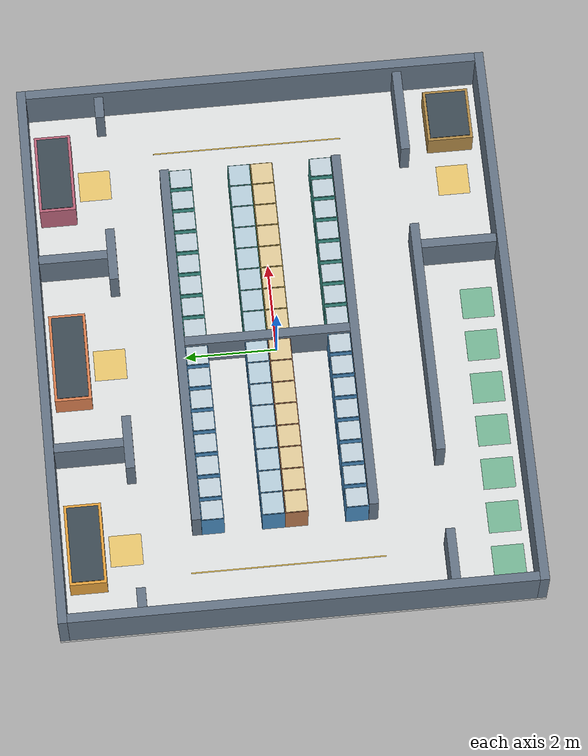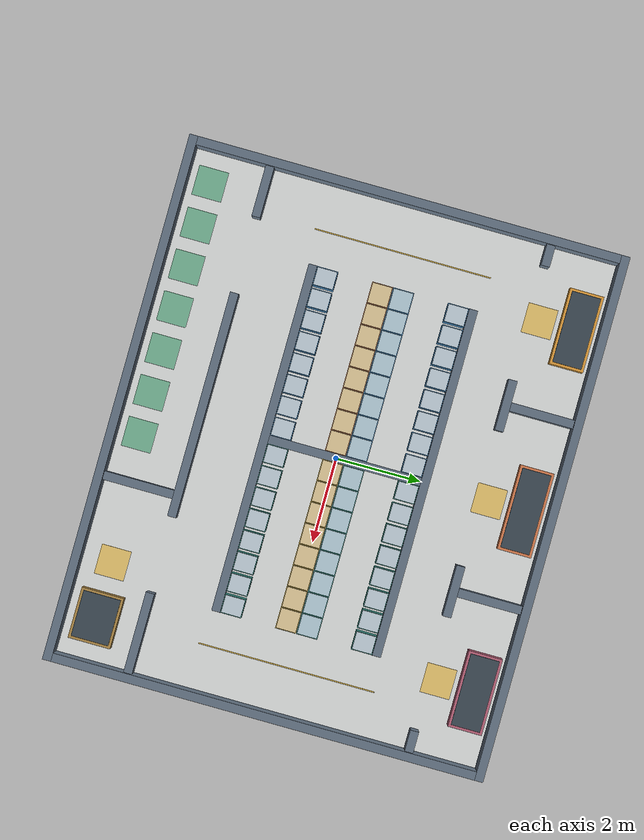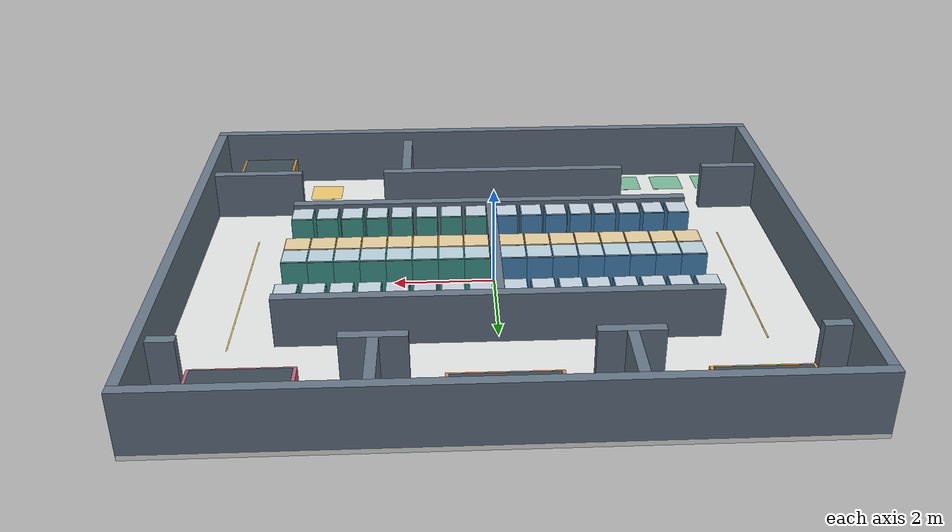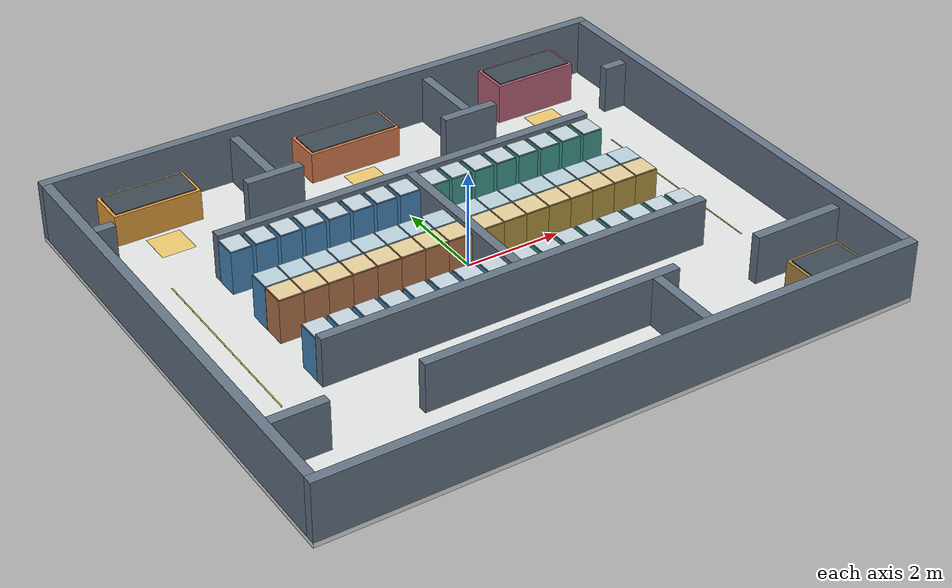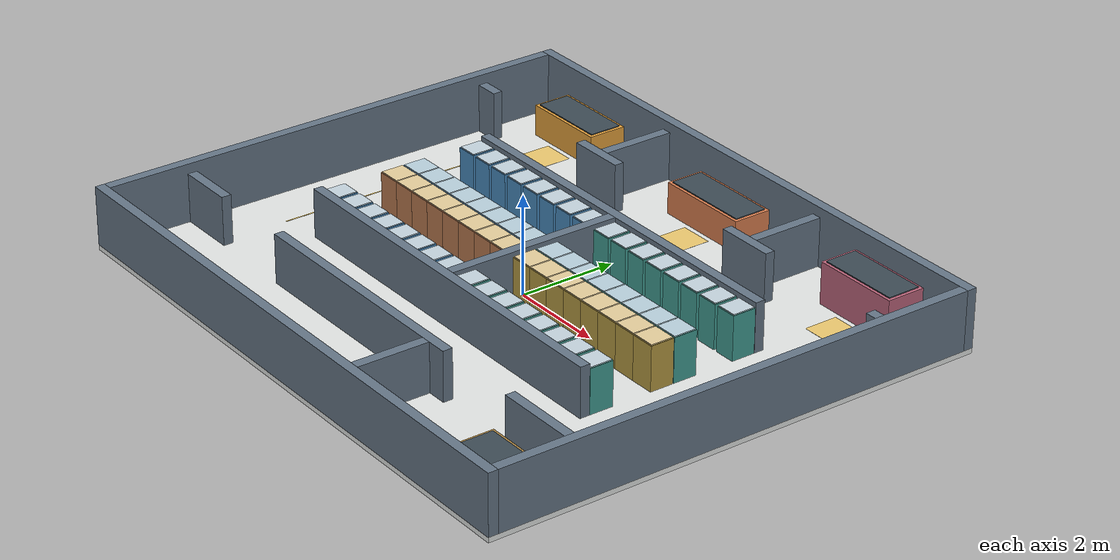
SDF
<?xml version='1.0' encoding='utf-8'?>
<sdf version="1.6">
  <world name="warehouse">
    <gravity>0 0 -9.8</gravity>
    <physics name="default_physics" type="ode">
      <max_step_size>0.001</max_step_size>
      <real_time_factor>1</real_time_factor>
      <real_time_update_rate>1000</real_time_update_rate>
    </physics>
    <plugin name="gazebo_ros_state" filename="libgazebo_ros_state.so">
      <ros>
        <namespace>/gazebo</namespace>
      </ros>
      <update_rate>30.0</update_rate>
    </plugin>
    <scene>
      <ambient>.7 .7 .7 1</ambient>
      <background>.88 .91 .94 1</background>
      <shadows>false</shadows>
    </scene>
    <light name="sun" type="directional">
      <pose>0 0 10 0 0 0</pose>
      <diffuse>.8 .8 .8 1</diffuse>
      <specular>.1 .1 .1 1</specular>
      <direction>-.3 .2 -1</direction>
      <cast_shadows>false</cast_shadows>
    </light>
    <model name="floor">
      <static>true</static>
      <link name="floor_link">
        <collision name="floor_collision">
          <pose>0 0 -.05 0 0 0</pose>
          <geometry>
            <box>
              <size>12.4 10.4 0.1</size>
            </box>
          </geometry>
        </collision>
        <visual name="floor_visual">
          <pose>0 0 -0.05 0 0 0</pose>
          <geometry>
            <box>
              <size>12.4 10.4 0.1</size>
            </box>
          </geometry>
          <material>
            <ambient>0.8901960784313725 0.9019607843137255 0.8980392156862745 1</ambient>
            <diffuse>0.8901960784313725 0.9019607843137255 0.8980392156862745 1</diffuse>
          </material>
          <cast_shadows>false</cast_shadows>
        </visual>
      </link>
    </model>
    <model name="wall_north">
      <static>true</static>
      <pose>0 5.1 0 0 0 0</pose>
      <link name="body">
        <collision name="collision">
          <pose>0 0 0.6 0 0 0</pose>
          <geometry>
            <box>
              <size>12.4 0.2 1.2</size>
            </box>
          </geometry>
        </collision>
        <visual name="visual">
          <pose>0 0 0.6 0 0 0</pose>
          <geometry>
            <box>
              <size>12.4 0.2 1.2</size>
            </box>
          </geometry>
          <material>
            <ambient>0.4 0.4627450980392157 0.5294117647058824 1</ambient>
            <diffuse>0.4 0.4627450980392157 0.5294117647058824 1</diffuse>
          </material>
          <cast_shadows>false</cast_shadows>
        </visual>
      </link>
    </model>
    <model name="wall_south">
      <static>true</static>
      <pose>0 -5.1 0 0 0 0</pose>
      <link name="body">
        <collision name="collision">
          <pose>0 0 0.6 0 0 0</pose>
          <geometry>
            <box>
              <size>12.4 0.2 1.2</size>
            </box>
          </geometry>
        </collision>
        <visual name="visual">
          <pose>0 0 0.6 0 0 0</pose>
          <geometry>
            <box>
              <size>12.4 0.2 1.2</size>
            </box>
          </geometry>
          <material>
            <ambient>0.4 0.4627450980392157 0.5294117647058824 1</ambient>
            <diffuse>0.4 0.4627450980392157 0.5294117647058824 1</diffuse>
          </material>
          <cast_shadows>false</cast_shadows>
        </visual>
      </link>
    </model>
    <model name="wall_west">
      <static>true</static>
      <pose>-6.1 0 0 0 0 0</pose>
      <link name="body">
        <collision name="collision">
          <pose>0 0 0.6 0 0 0</pose>
          <geometry>
            <box>
              <size>0.2 10 1.2</size>
            </box>
          </geometry>
        </collision>
        <visual name="visual">
          <pose>0 0 0.6 0 0 0</pose>
          <geometry>
            <box>
              <size>0.2 10 1.2</size>
            </box>
          </geometry>
          <material>
            <ambient>0.4 0.4627450980392157 0.5294117647058824 1</ambient>
            <diffuse>0.4 0.4627450980392157 0.5294117647058824 1</diffuse>
          </material>
          <cast_shadows>false</cast_shadows>
        </visual>
      </link>
    </model>
    <model name="wall_east">
      <static>true</static>
      <pose>6.1 0 0 0 0 0</pose>
      <link name="body">
        <collision name="collision">
          <pose>0 0 0.6 0 0 0</pose>
          <geometry>
            <box>
              <size>0.2 10 1.2</size>
            </box>
          </geometry>
        </collision>
        <visual name="visual">
          <pose>0 0 0.6 0 0 0</pose>
          <geometry>
            <box>
              <size>0.2 10 1.2</size>
            </box>
          </geometry>
          <material>
            <ambient>0.4 0.4627450980392157 0.5294117647058824 1</ambient>
            <diffuse>0.4 0.4627450980392157 0.5294117647058824 1</diffuse>
          </material>
          <cast_shadows>false</cast_shadows>
        </visual>
      </link>
    </model>
    <model name="partition_west">
      <static>true</static>
      <pose>-5.4 -3.25 0 0 0 0</pose>
      <link name="body">
        <collision name="collision">
          <pose>0 0 0.5 0 0 0</pose>
          <geometry>
            <box>
              <size>1.2 0.2 1.0</size>
            </box>
          </geometry>
        </collision>
        <visual name="visual">
          <pose>0 0 0.5 0 0 0</pose>
          <geometry>
            <box>
              <size>1.2 0.2 1.0</size>
            </box>
          </geometry>
          <material>
            <ambient>0.4 0.4627450980392157 0.5294117647058824 1</ambient>
            <diffuse>0.4 0.4627450980392157 0.5294117647058824 1</diffuse>
          </material>
          <cast_shadows>false</cast_shadows>
        </visual>
      </link>
    </model>
    <model name="partition_middle">
      <static>true</static>
      <pose>-0.35 -3.25 0 0 0 0</pose>
      <link name="body">
        <collision name="collision">
          <pose>0 0 0.5 0 0 0</pose>
          <geometry>
            <box>
              <size>5.3 0.2 1.0</size>
            </box>
          </geometry>
        </collision>
        <visual name="visual">
          <pose>0 0 0.5 0 0 0</pose>
          <geometry>
            <box>
              <size>5.3 0.2 1.0</size>
            </box>
          </geometry>
          <material>
            <ambient>0.4 0.4627450980392157 0.5294117647058824 1</ambient>
            <diffuse>0.4 0.4627450980392157 0.5294117647058824 1</diffuse>
          </material>
          <cast_shadows>false</cast_shadows>
        </visual>
      </link>
    </model>
    <model name="partition_east">
      <static>true</static>
      <pose>5.05 -3.25 0 0 0 0</pose>
      <link name="body">
        <collision name="collision">
          <pose>0 0 0.5 0 0 0</pose>
          <geometry>
            <box>
              <size>1.9 0.2 1.0</size>
            </box>
          </geometry>
        </collision>
        <visual name="visual">
          <pose>0 0 0.5 0 0 0</pose>
          <geometry>
            <box>
              <size>1.9 0.2 1.0</size>
            </box>
          </geometry>
          <material>
            <ambient>0.4 0.4627450980392157 0.5294117647058824 1</ambient>
            <diffuse>0.4 0.4627450980392157 0.5294117647058824 1</diffuse>
          </material>
          <cast_shadows>false</cast_shadows>
        </visual>
      </link>
    </model>
    <model name="storage_north">
      <static>true</static>
      <pose>0 2.1 0 0 0 0</pose>
      <link name="body">
        <collision name="collision">
          <pose>0 0 0.5 0 0 0</pose>
          <geometry>
            <box>
              <size>8.2 0.2 1.0</size>
            </box>
          </geometry>
        </collision>
        <visual name="visual">
          <pose>0 0 0.5 0 0 0</pose>
          <geometry>
            <box>
              <size>8.2 0.2 1.0</size>
            </box>
          </geometry>
          <material>
            <ambient>0.4 0.4627450980392157 0.5294117647058824 1</ambient>
            <diffuse>0.4 0.4627450980392157 0.5294117647058824 1</diffuse>
          </material>
          <cast_shadows>false</cast_shadows>
        </visual>
      </link>
    </model>
    <model name="storage_south">
      <static>true</static>
      <pose>0 -1.7 0 0 0 0</pose>
      <link name="body">
        <collision name="collision">
          <pose>0 0 0.5 0 0 0</pose>
          <geometry>
            <box>
              <size>8.2 0.2 1.0</size>
            </box>
          </geometry>
        </collision>
        <visual name="visual">
          <pose>0 0 0.5 0 0 0</pose>
          <geometry>
            <box>
              <size>8.2 0.2 1.0</size>
            </box>
          </geometry>
          <material>
            <ambient>0.4 0.4627450980392157 0.5294117647058824 1</ambient>
            <diffuse>0.4 0.4627450980392157 0.5294117647058824 1</diffuse>
          </material>
          <cast_shadows>false</cast_shadows>
        </visual>
      </link>
    </model>
    <model name="storage_divider">
      <static>true</static>
      <pose>0 0.2 0 0 0 0</pose>
      <link name="body">
        <collision name="collision">
          <pose>0 0 0.5 0 0 0</pose>
          <geometry>
            <box>
              <size>0.2 3.6 1.0</size>
            </box>
          </geometry>
        </collision>
        <visual name="visual">
          <pose>0 0 0.5 0 0 0</pose>
          <geometry>
            <box>
              <size>0.2 3.6 1.0</size>
            </box>
          </geometry>
          <material>
            <ambient>0.4 0.4627450980392157 0.5294117647058824 1</ambient>
            <diffuse>0.4 0.4627450980392157 0.5294117647058824 1</diffuse>
          </material>
          <cast_shadows>false</cast_shadows>
        </visual>
      </link>
    </model>
    <model name="work_divider_w">
      <static>true</static>
      <pose>-2.2 4.25 0 0 0 0</pose>
      <link name="body">
        <collision name="collision">
          <pose>0 0 0.5 0 0 0</pose>
          <geometry>
            <box>
              <size>0.2 1.5 1.0</size>
            </box>
          </geometry>
        </collision>
        <visual name="visual">
          <pose>0 0 0.5 0 0 0</pose>
          <geometry>
            <box>
              <size>0.2 1.5 1.0</size>
            </box>
          </geometry>
          <material>
            <ambient>0.4 0.4627450980392157 0.5294117647058824 1</ambient>
            <diffuse>0.4 0.4627450980392157 0.5294117647058824 1</diffuse>
          </material>
          <cast_shadows>false</cast_shadows>
        </visual>
      </link>
    </model>
    <model name="work_divider_e">
      <static>true</static>
      <pose>2.2 4.25 0 0 0 0</pose>
      <link name="body">
        <collision name="collision">
          <pose>0 0 0.5 0 0 0</pose>
          <geometry>
            <box>
              <size>0.2 1.5 1.0</size>
            </box>
          </geometry>
        </collision>
        <visual name="visual">
          <pose>0 0 0.5 0 0 0</pose>
          <geometry>
            <box>
              <size>0.2 1.5 1.0</size>
            </box>
          </geometry>
          <material>
            <ambient>0.4 0.4627450980392157 0.5294117647058824 1</ambient>
            <diffuse>0.4 0.4627450980392157 0.5294117647058824 1</diffuse>
          </material>
          <cast_shadows>false</cast_shadows>
        </visual>
      </link>
    </model>
    <model name="work_wing_w">
      <static>true</static>
      <pose>-2.2 3.4 0 0 0 0</pose>
      <link name="body">
        <collision name="collision">
          <pose>0 0 0.5 0 0 0</pose>
          <geometry>
            <box>
              <size>1.2 0.2 1.0</size>
            </box>
          </geometry>
        </collision>
        <visual name="visual">
          <pose>0 0 0.5 0 0 0</pose>
          <geometry>
            <box>
              <size>1.2 0.2 1.0</size>
            </box>
          </geometry>
          <material>
            <ambient>0.4 0.4627450980392157 0.5294117647058824 1</ambient>
            <diffuse>0.4 0.4627450980392157 0.5294117647058824 1</diffuse>
          </material>
          <cast_shadows>false</cast_shadows>
        </visual>
      </link>
    </model>
    <model name="work_wing_e">
      <static>true</static>
      <pose>2.2 3.4 0 0 0 0</pose>
      <link name="body">
        <collision name="collision">
          <pose>0 0 0.5 0 0 0</pose>
          <geometry>
            <box>
              <size>1.2 0.2 1.0</size>
            </box>
          </geometry>
        </collision>
        <visual name="visual">
          <pose>0 0 0.5 0 0 0</pose>
          <geometry>
            <box>
              <size>1.2 0.2 1.0</size>
            </box>
          </geometry>
          <material>
            <ambient>0.4 0.4627450980392157 0.5294117647058824 1</ambient>
            <diffuse>0.4 0.4627450980392157 0.5294117647058824 1</diffuse>
          </material>
          <cast_shadows>false</cast_shadows>
        </visual>
      </link>
    </model>
    <model name="work_stub_w">
      <static>true</static>
      <pose>-5.75 3.4 0 0 0 0</pose>
      <link name="body">
        <collision name="collision">
          <pose>0 0 0.5 0 0 0</pose>
          <geometry>
            <box>
              <size>0.5 0.2 1.0</size>
            </box>
          </geometry>
        </collision>
        <visual name="visual">
          <pose>0 0 0.5 0 0 0</pose>
          <geometry>
            <box>
              <size>0.5 0.2 1.0</size>
            </box>
          </geometry>
          <material>
            <ambient>0.4 0.4627450980392157 0.5294117647058824 1</ambient>
            <diffuse>0.4 0.4627450980392157 0.5294117647058824 1</diffuse>
          </material>
          <cast_shadows>false</cast_shadows>
        </visual>
      </link>
    </model>
    <model name="work_stub_e">
      <static>true</static>
      <pose>5.75 3.4 0 0 0 0</pose>
      <link name="body">
        <collision name="collision">
          <pose>0 0 0.5 0 0 0</pose>
          <geometry>
            <box>
              <size>0.5 0.2 1.0</size>
            </box>
          </geometry>
        </collision>
        <visual name="visual">
          <pose>0 0 0.5 0 0 0</pose>
          <geometry>
            <box>
              <size>0.5 0.2 1.0</size>
            </box>
          </geometry>
          <material>
            <ambient>0.4 0.4627450980392157 0.5294117647058824 1</ambient>
            <diffuse>0.4 0.4627450980392157 0.5294117647058824 1</diffuse>
          </material>
          <cast_shadows>false</cast_shadows>
        </visual>
      </link>
    </model>
    <model name="shipping_divider">
      <static>true</static>
      <pose>1.8 -4.175 0 0 0 0</pose>
      <link name="body">
        <collision name="collision">
          <pose>0 0 0.5 0 0 0</pose>
          <geometry>
            <box>
              <size>0.2 1.65 1.0</size>
            </box>
          </geometry>
        </collision>
        <visual name="visual">
          <pose>0 0 0.5 0 0 0</pose>
          <geometry>
            <box>
              <size>0.2 1.65 1.0</size>
            </box>
          </geometry>
          <material>
            <ambient>0.4 0.4627450980392157 0.5294117647058824 1</ambient>
            <diffuse>0.4 0.4627450980392157 0.5294117647058824 1</diffuse>
          </material>
          <cast_shadows>false</cast_shadows>
        </visual>
      </link>
    </model>
    <model name="receiving">
      <static>true</static>
      <pose>-4.3 4.5 0 0 0 0</pose>
      <link name="body">
        <collision name="collision">
          <pose>0 0 0.325 0 0 0</pose>
          <geometry>
            <box>
              <size>1.8 0.8 0.65</size>
            </box>
          </geometry>
        </collision>
        <visual name="visual">
          <pose>0 0 0.325 0 0 0</pose>
          <geometry>
            <box>
              <size>1.8 0.8 0.65</size>
            </box>
          </geometry>
          <material>
            <ambient>0.9019607843137255 0.6352941176470588 0.23529411764705882 1</ambient>
            <diffuse>0.9019607843137255 0.6352941176470588 0.23529411764705882 1</diffuse>
          </material>
          <cast_shadows>false</cast_shadows>
        </visual>
        <visual name="work_surface">
          <pose>0 0 0.66 0 0 0</pose>
          <geometry>
            <box>
              <size>1.6800000000000002 0.68 0.02</size>
            </box>
          </geometry>
          <material>
            <ambient>0.23921568627450981 0.29411764705882354 0.3333333333333333 1</ambient>
            <diffuse>0.23921568627450981 0.29411764705882354 0.3333333333333333 1</diffuse>
          </material>
          <cast_shadows>false</cast_shadows>
        </visual>
      </link>
    </model>
    <model name="conveyor">
      <static>true</static>
      <pose>0 4.5 0 0 0 0</pose>
      <link name="body">
        <collision name="collision">
          <pose>0 0 0.325 0 0 0</pose>
          <geometry>
            <box>
              <size>2.0 0.8 0.65</size>
            </box>
          </geometry>
        </collision>
        <visual name="visual">
          <pose>0 0 0.325 0 0 0</pose>
          <geometry>
            <box>
              <size>2.0 0.8 0.65</size>
            </box>
          </geometry>
          <material>
            <ambient>0.8627450980392157 0.5019607843137255 0.3137254901960784 1</ambient>
            <diffuse>0.8627450980392157 0.5019607843137255 0.3137254901960784 1</diffuse>
          </material>
          <cast_shadows>false</cast_shadows>
        </visual>
        <visual name="work_surface">
          <pose>0 0 0.66 0 0 0</pose>
          <geometry>
            <box>
              <size>1.88 0.68 0.02</size>
            </box>
          </geometry>
          <material>
            <ambient>0.23921568627450981 0.29411764705882354 0.3333333333333333 1</ambient>
            <diffuse>0.23921568627450981 0.29411764705882354 0.3333333333333333 1</diffuse>
          </material>
          <cast_shadows>false</cast_shadows>
        </visual>
      </link>
    </model>
    <model name="machine">
      <static>true</static>
      <pose>4.3 4.5 0 0 0 0</pose>
      <link name="body">
        <collision name="collision">
          <pose>0 0 0.425 0 0 0</pose>
          <geometry>
            <box>
              <size>1.8 0.8 0.85</size>
            </box>
          </geometry>
        </collision>
        <visual name="visual">
          <pose>0 0 0.425 0 0 0</pose>
          <geometry>
            <box>
              <size>1.8 0.8 0.85</size>
            </box>
          </geometry>
          <material>
            <ambient>0.7372549019607844 0.39215686274509803 0.4823529411764706 1</ambient>
            <diffuse>0.7372549019607844 0.39215686274509803 0.4823529411764706 1</diffuse>
          </material>
          <cast_shadows>false</cast_shadows>
        </visual>
        <visual name="work_surface">
          <pose>0 0 0.86 0 0 0</pose>
          <geometry>
            <box>
              <size>1.6800000000000002 0.68 0.02</size>
            </box>
          </geometry>
          <material>
            <ambient>0.23921568627450981 0.29411764705882354 0.3333333333333333 1</ambient>
            <diffuse>0.23921568627450981 0.29411764705882354 0.3333333333333333 1</diffuse>
          </material>
          <cast_shadows>false</cast_shadows>
        </visual>
      </link>
    </model>
    <model name="shipping">
      <static>true</static>
      <pose>5 -4.3 0 0 0 0</pose>
      <link name="body">
        <collision name="collision">
          <pose>0 0 0.325 0 0 0</pose>
          <geometry>
            <box>
              <size>1.2 1.0 0.65</size>
            </box>
          </geometry>
        </collision>
        <visual name="visual">
          <pose>0 0 0.325 0 0 0</pose>
          <geometry>
            <box>
              <size>1.2 1.0 0.65</size>
            </box>
          </geometry>
          <material>
            <ambient>0.6980392156862745 0.5450980392156862 0.2784313725490196 1</ambient>
            <diffuse>0.6980392156862745 0.5450980392156862 0.2784313725490196 1</diffuse>
          </material>
          <cast_shadows>false</cast_shadows>
        </visual>
        <visual name="work_surface">
          <pose>0 0 0.66 0 0 0</pose>
          <geometry>
            <box>
              <size>1.08 0.88 0.02</size>
            </box>
          </geometry>
          <material>
            <ambient>0.23921568627450981 0.29411764705882354 0.3333333333333333 1</ambient>
            <diffuse>0.23921568627450981 0.29411764705882354 0.3333333333333333 1</diffuse>
          </material>
          <cast_shadows>false</cast_shadows>
        </visual>
      </link>
    </model>
    <model name="rack_A1_1">
      <static>true</static>
      <pose>-3.8799999999999994 -1.35 0 0 0 0</pose>
      <link name="body">
        <collision name="collision">
          <pose>0 0 0.45 0 0 0</pose>
          <geometry>
            <box>
              <size>0.44 0.5 0.9</size>
            </box>
          </geometry>
        </collision>
        <visual name="bay_single">
          <pose>0 0 0.45 0 0 0</pose>
          <geometry>
            <box>
              <size>0.44 0.49 0.9</size>
            </box>
          </geometry>
          <material>
            <ambient>0.2823529411764706 0.5490196078431373 0.7529411764705882 1</ambient>
            <diffuse>0.2823529411764706 0.5490196078431373 0.7529411764705882 1</diffuse>
          </material>
          <cast_shadows>false</cast_shadows>
        </visual>
        <visual name="cap_single">
          <pose>0 0 0.91 0 0 0</pose>
          <geometry>
            <box>
              <size>0.41000000000000003 0.46 0.02</size>
            </box>
          </geometry>
          <material>
            <ambient>0.7764705882352941 0.8352941176470589 0.8745098039215686 1</ambient>
            <diffuse>0.7764705882352941 0.8352941176470589 0.8745098039215686 1</diffuse>
          </material>
          <cast_shadows>false</cast_shadows>
        </visual>
      </link>
    </model>
    <model name="rack_A1_2">
      <static>true</static>
      <pose>-3.371428571428571 -1.35 0 0 0 0</pose>
      <link name="body">
        <collision name="collision">
          <pose>0 0 0.45 0 0 0</pose>
          <geometry>
            <box>
              <size>0.44 0.5 0.9</size>
            </box>
          </geometry>
        </collision>
        <visual name="bay_single">
          <pose>0 0 0.45 0 0 0</pose>
          <geometry>
            <box>
              <size>0.44 0.49 0.9</size>
            </box>
          </geometry>
          <material>
            <ambient>0.2823529411764706 0.5490196078431373 0.7529411764705882 1</ambient>
            <diffuse>0.2823529411764706 0.5490196078431373 0.7529411764705882 1</diffuse>
          </material>
          <cast_shadows>false</cast_shadows>
        </visual>
        <visual name="cap_single">
          <pose>0 0 0.91 0 0 0</pose>
          <geometry>
            <box>
              <size>0.41000000000000003 0.46 0.02</size>
            </box>
          </geometry>
          <material>
            <ambient>0.7764705882352941 0.8352941176470589 0.8745098039215686 1</ambient>
            <diffuse>0.7764705882352941 0.8352941176470589 0.8745098039215686 1</diffuse>
          </material>
          <cast_shadows>false</cast_shadows>
        </visual>
      </link>
    </model>
    <model name="rack_A1_3">
      <static>true</static>
      <pose>-2.862857142857142 -1.35 0 0 0 0</pose>
      <link name="body">
        <collision name="collision">
          <pose>0 0 0.45 0 0 0</pose>
          <geometry>
            <box>
              <size>0.44 0.5 0.9</size>
            </box>
          </geometry>
        </collision>
        <visual name="bay_single">
          <pose>0 0 0.45 0 0 0</pose>
          <geometry>
            <box>
              <size>0.44 0.49 0.9</size>
            </box>
          </geometry>
          <material>
            <ambient>0.2823529411764706 0.5490196078431373 0.7529411764705882 1</ambient>
            <diffuse>0.2823529411764706 0.5490196078431373 0.7529411764705882 1</diffuse>
          </material>
          <cast_shadows>false</cast_shadows>
        </visual>
        <visual name="cap_single">
          <pose>0 0 0.91 0 0 0</pose>
          <geometry>
            <box>
              <size>0.41000000000000003 0.46 0.02</size>
            </box>
          </geometry>
          <material>
            <ambient>0.7764705882352941 0.8352941176470589 0.8745098039215686 1</ambient>
            <diffuse>0.7764705882352941 0.8352941176470589 0.8745098039215686 1</diffuse>
          </material>
          <cast_shadows>false</cast_shadows>
        </visual>
      </link>
    </model>
    <model name="rack_A1_4">
      <static>true</static>
      <pose>-2.3542857142857136 -1.35 0 0 0 0</pose>
      <link name="body">
        <collision name="collision">
          <pose>0 0 0.45 0 0 0</pose>
          <geometry>
            <box>
              <size>0.44 0.5 0.9</size>
            </box>
          </geometry>
        </collision>
        <visual name="bay_single">
          <pose>0 0 0.45 0 0 0</pose>
          <geometry>
            <box>
              <size>0.44 0.49 0.9</size>
            </box>
          </geometry>
          <material>
            <ambient>0.2823529411764706 0.5490196078431373 0.7529411764705882 1</ambient>
            <diffuse>0.2823529411764706 0.5490196078431373 0.7529411764705882 1</diffuse>
          </material>
          <cast_shadows>false</cast_shadows>
        </visual>
        <visual name="cap_single">
          <pose>0 0 0.91 0 0 0</pose>
          <geometry>
            <box>
              <size>0.41000000000000003 0.46 0.02</size>
            </box>
          </geometry>
          <material>
            <ambient>0.7764705882352941 0.8352941176470589 0.8745098039215686 1</ambient>
            <diffuse>0.7764705882352941 0.8352941176470589 0.8745098039215686 1</diffuse>
          </material>
          <cast_shadows>false</cast_shadows>
        </visual>
      </link>
    </model>
    <model name="rack_A1_5">
      <static>true</static>
      <pose>-1.8457142857142852 -1.35 0 0 0 0</pose>
      <link name="body">
        <collision name="collision">
          <pose>0 0 0.45 0 0 0</pose>
          <geometry>
            <box>
              <size>0.44 0.5 0.9</size>
            </box>
          </geometry>
        </collision>
        <visual name="bay_single">
          <pose>0 0 0.45 0 0 0</pose>
          <geometry>
            <box>
              <size>0.44 0.49 0.9</size>
            </box>
          </geometry>
          <material>
            <ambient>0.2823529411764706 0.5490196078431373 0.7529411764705882 1</ambient>
            <diffuse>0.2823529411764706 0.5490196078431373 0.7529411764705882 1</diffuse>
          </material>
          <cast_shadows>false</cast_shadows>
        </visual>
        <visual name="cap_single">
          <pose>0 0 0.91 0 0 0</pose>
          <geometry>
            <box>
              <size>0.41000000000000003 0.46 0.02</size>
            </box>
          </geometry>
          <material>
            <ambient>0.7764705882352941 0.8352941176470589 0.8745098039215686 1</ambient>
            <diffuse>0.7764705882352941 0.8352941176470589 0.8745098039215686 1</diffuse>
          </material>
          <cast_shadows>false</cast_shadows>
        </visual>
      </link>
    </model>
    <model name="rack_A1_6">
      <static>true</static>
      <pose>-1.3371428571428567 -1.35 0 0 0 0</pose>
      <link name="body">
        <collision name="collision">
          <pose>0 0 0.45 0 0 0</pose>
          <geometry>
            <box>
              <size>0.44 0.5 0.9</size>
            </box>
          </geometry>
        </collision>
        <visual name="bay_single">
          <pose>0 0 0.45 0 0 0</pose>
          <geometry>
            <box>
              <size>0.44 0.49 0.9</size>
            </box>
          </geometry>
          <material>
            <ambient>0.2823529411764706 0.5490196078431373 0.7529411764705882 1</ambient>
            <diffuse>0.2823529411764706 0.5490196078431373 0.7529411764705882 1</diffuse>
          </material>
          <cast_shadows>false</cast_shadows>
        </visual>
        <visual name="cap_single">
          <pose>0 0 0.91 0 0 0</pose>
          <geometry>
            <box>
              <size>0.41000000000000003 0.46 0.02</size>
            </box>
          </geometry>
          <material>
            <ambient>0.7764705882352941 0.8352941176470589 0.8745098039215686 1</ambient>
            <diffuse>0.7764705882352941 0.8352941176470589 0.8745098039215686 1</diffuse>
          </material>
          <cast_shadows>false</cast_shadows>
        </visual>
      </link>
    </model>
    <model name="rack_A1_7">
      <static>true</static>
      <pose>-0.8285714285714278 -1.35 0 0 0 0</pose>
      <link name="body">
        <collision name="collision">
          <pose>0 0 0.45 0 0 0</pose>
          <geometry>
            <box>
              <size>0.44 0.5 0.9</size>
            </box>
          </geometry>
        </collision>
        <visual name="bay_single">
          <pose>0 0 0.45 0 0 0</pose>
          <geometry>
            <box>
              <size>0.44 0.49 0.9</size>
            </box>
          </geometry>
          <material>
            <ambient>0.2823529411764706 0.5490196078431373 0.7529411764705882 1</ambient>
            <diffuse>0.2823529411764706 0.5490196078431373 0.7529411764705882 1</diffuse>
          </material>
          <cast_shadows>false</cast_shadows>
        </visual>
        <visual name="cap_single">
          <pose>0 0 0.91 0 0 0</pose>
          <geometry>
            <box>
              <size>0.41000000000000003 0.46 0.02</size>
            </box>
          </geometry>
          <material>
            <ambient>0.7764705882352941 0.8352941176470589 0.8745098039215686 1</ambient>
            <diffuse>0.7764705882352941 0.8352941176470589 0.8745098039215686 1</diffuse>
          </material>
          <cast_shadows>false</cast_shadows>
        </visual>
      </link>
    </model>
    <model name="rack_A1_8">
      <static>true</static>
      <pose>-0.3199999999999994 -1.35 0 0 0 0</pose>
      <link name="body">
        <collision name="collision">
          <pose>0 0 0.45 0 0 0</pose>
          <geometry>
            <box>
              <size>0.44 0.5 0.9</size>
            </box>
          </geometry>
        </collision>
        <visual name="bay_single">
          <pose>0 0 0.45 0 0 0</pose>
          <geometry>
            <box>
              <size>0.44 0.49 0.9</size>
            </box>
          </geometry>
          <material>
            <ambient>0.2823529411764706 0.5490196078431373 0.7529411764705882 1</ambient>
            <diffuse>0.2823529411764706 0.5490196078431373 0.7529411764705882 1</diffuse>
          </material>
          <cast_shadows>false</cast_shadows>
        </visual>
        <visual name="cap_single">
          <pose>0 0 0.91 0 0 0</pose>
          <geometry>
            <box>
              <size>0.41000000000000003 0.46 0.02</size>
            </box>
          </geometry>
          <material>
            <ambient>0.7764705882352941 0.8352941176470589 0.8745098039215686 1</ambient>
            <diffuse>0.7764705882352941 0.8352941176470589 0.8745098039215686 1</diffuse>
          </material>
          <cast_shadows>false</cast_shadows>
        </visual>
      </link>
    </model>
    <model name="rack_A2_1">
      <static>true</static>
      <pose>-3.8499999999999996 0.2 0 0 0 0</pose>
      <link name="body">
        <collision name="collision">
          <pose>0 0 0.45 0 0 0</pose>
          <geometry>
            <box>
              <size>0.5 1.0 0.9</size>
            </box>
          </geometry>
        </collision>
        <visual name="bay_north">
          <pose>0 0.25 0.45 0 0 0</pose>
          <geometry>
            <box>
              <size>0.5 0.49 0.9</size>
            </box>
          </geometry>
          <material>
            <ambient>0.2823529411764706 0.5490196078431373 0.7529411764705882 1</ambient>
            <diffuse>0.2823529411764706 0.5490196078431373 0.7529411764705882 1</diffuse>
          </material>
          <cast_shadows>false</cast_shadows>
        </visual>
        <visual name="cap_north">
          <pose>0 0.25 0.91 0 0 0</pose>
          <geometry>
            <box>
              <size>0.47 0.46 0.02</size>
            </box>
          </geometry>
          <material>
            <ambient>0.7294117647058823 0.8235294117647058 0.8705882352941177 1</ambient>
            <diffuse>0.7294117647058823 0.8235294117647058 0.8705882352941177 1</diffuse>
          </material>
          <cast_shadows>false</cast_shadows>
        </visual>
        <visual name="bay_south">
          <pose>0 -0.25 0.45 0 0 0</pose>
          <geometry>
            <box>
              <size>0.5 0.49 0.9</size>
            </box>
          </geometry>
          <material>
            <ambient>0.7254901960784313 0.4745098039215686 0.3137254901960784 1</ambient>
            <diffuse>0.7254901960784313 0.4745098039215686 0.3137254901960784 1</diffuse>
          </material>
          <cast_shadows>false</cast_shadows>
        </visual>
        <visual name="cap_south">
          <pose>0 -0.25 0.91 0 0 0</pose>
          <geometry>
            <box>
              <size>0.47 0.46 0.02</size>
            </box>
          </geometry>
          <material>
            <ambient>0.9019607843137255 0.8117647058823529 0.615686274509804 1</ambient>
            <diffuse>0.9019607843137255 0.8117647058823529 0.615686274509804 1</diffuse>
          </material>
          <cast_shadows>false</cast_shadows>
        </visual>
      </link>
    </model>
    <model name="rack_A2_2">
      <static>true</static>
      <pose>-3.3499999999999996 0.2 0 0 0 0</pose>
      <link name="body">
        <collision name="collision">
          <pose>0 0 0.45 0 0 0</pose>
          <geometry>
            <box>
              <size>0.5 1.0 0.9</size>
            </box>
          </geometry>
        </collision>
        <visual name="bay_north">
          <pose>0 0.25 0.45 0 0 0</pose>
          <geometry>
            <box>
              <size>0.5 0.49 0.9</size>
            </box>
          </geometry>
          <material>
            <ambient>0.2823529411764706 0.5490196078431373 0.7529411764705882 1</ambient>
            <diffuse>0.2823529411764706 0.5490196078431373 0.7529411764705882 1</diffuse>
          </material>
          <cast_shadows>false</cast_shadows>
        </visual>
        <visual name="cap_north">
          <pose>0 0.25 0.91 0 0 0</pose>
          <geometry>
            <box>
              <size>0.47 0.46 0.02</size>
            </box>
          </geometry>
          <material>
            <ambient>0.7294117647058823 0.8235294117647058 0.8705882352941177 1</ambient>
            <diffuse>0.7294117647058823 0.8235294117647058 0.8705882352941177 1</diffuse>
          </material>
          <cast_shadows>false</cast_shadows>
        </visual>
        <visual name="bay_south">
          <pose>0 -0.25 0.45 0 0 0</pose>
          <geometry>
            <box>
              <size>0.5 0.49 0.9</size>
            </box>
          </geometry>
          <material>
            <ambient>0.7254901960784313 0.4745098039215686 0.3137254901960784 1</ambient>
            <diffuse>0.7254901960784313 0.4745098039215686 0.3137254901960784 1</diffuse>
          </material>
          <cast_shadows>false</cast_shadows>
        </visual>
        <visual name="cap_south">
          <pose>0 -0.25 0.91 0 0 0</pose>
          <geometry>
            <box>
              <size>0.47 0.46 0.02</size>
            </box>
          </geometry>
          <material>
            <ambient>0.9019607843137255 0.8117647058823529 0.615686274509804 1</ambient>
            <diffuse>0.9019607843137255 0.8117647058823529 0.615686274509804 1</diffuse>
          </material>
          <cast_shadows>false</cast_shadows>
        </visual>
      </link>
    </model>
    <model name="rack_A2_3">
      <static>true</static>
      <pose>-2.8499999999999996 0.2 0 0 0 0</pose>
      <link name="body">
        <collision name="collision">
          <pose>0 0 0.45 0 0 0</pose>
          <geometry>
            <box>
              <size>0.5 1.0 0.9</size>
            </box>
          </geometry>
        </collision>
        <visual name="bay_north">
          <pose>0 0.25 0.45 0 0 0</pose>
          <geometry>
            <box>
              <size>0.5 0.49 0.9</size>
            </box>
          </geometry>
          <material>
            <ambient>0.2823529411764706 0.5490196078431373 0.7529411764705882 1</ambient>
            <diffuse>0.2823529411764706 0.5490196078431373 0.7529411764705882 1</diffuse>
          </material>
          <cast_shadows>false</cast_shadows>
        </visual>
        <visual name="cap_north">
          <pose>0 0.25 0.91 0 0 0</pose>
          <geometry>
            <box>
              <size>0.47 0.46 0.02</size>
            </box>
          </geometry>
          <material>
            <ambient>0.7294117647058823 0.8235294117647058 0.8705882352941177 1</ambient>
            <diffuse>0.7294117647058823 0.8235294117647058 0.8705882352941177 1</diffuse>
          </material>
          <cast_shadows>false</cast_shadows>
        </visual>
        <visual name="bay_south">
          <pose>0 -0.25 0.45 0 0 0</pose>
          <geometry>
            <box>
              <size>0.5 0.49 0.9</size>
            </box>
          </geometry>
          <material>
            <ambient>0.7254901960784313 0.4745098039215686 0.3137254901960784 1</ambient>
            <diffuse>0.7254901960784313 0.4745098039215686 0.3137254901960784 1</diffuse>
          </material>
          <cast_shadows>false</cast_shadows>
        </visual>
        <visual name="cap_south">
          <pose>0 -0.25 0.91 0 0 0</pose>
          <geometry>
            <box>
              <size>0.47 0.46 0.02</size>
            </box>
          </geometry>
          <material>
            <ambient>0.9019607843137255 0.8117647058823529 0.615686274509804 1</ambient>
            <diffuse>0.9019607843137255 0.8117647058823529 0.615686274509804 1</diffuse>
          </material>
          <cast_shadows>false</cast_shadows>
        </visual>
      </link>
    </model>
    <model name="rack_A2_4">
      <static>true</static>
      <pose>-2.3499999999999996 0.2 0 0 0 0</pose>
      <link name="body">
        <collision name="collision">
          <pose>0 0 0.45 0 0 0</pose>
          <geometry>
            <box>
              <size>0.5 1.0 0.9</size>
            </box>
          </geometry>
        </collision>
        <visual name="bay_north">
          <pose>0 0.25 0.45 0 0 0</pose>
          <geometry>
            <box>
              <size>0.5 0.49 0.9</size>
            </box>
          </geometry>
          <material>
            <ambient>0.2823529411764706 0.5490196078431373 0.7529411764705882 1</ambient>
            <diffuse>0.2823529411764706 0.5490196078431373 0.7529411764705882 1</diffuse>
          </material>
          <cast_shadows>false</cast_shadows>
        </visual>
        <visual name="cap_north">
          <pose>0 0.25 0.91 0 0 0</pose>
          <geometry>
            <box>
              <size>0.47 0.46 0.02</size>
            </box>
          </geometry>
          <material>
            <ambient>0.7294117647058823 0.8235294117647058 0.8705882352941177 1</ambient>
            <diffuse>0.7294117647058823 0.8235294117647058 0.8705882352941177 1</diffuse>
          </material>
          <cast_shadows>false</cast_shadows>
        </visual>
        <visual name="bay_south">
          <pose>0 -0.25 0.45 0 0 0</pose>
          <geometry>
            <box>
              <size>0.5 0.49 0.9</size>
            </box>
          </geometry>
          <material>
            <ambient>0.7254901960784313 0.4745098039215686 0.3137254901960784 1</ambient>
            <diffuse>0.7254901960784313 0.4745098039215686 0.3137254901960784 1</diffuse>
          </material>
          <cast_shadows>false</cast_shadows>
        </visual>
        <visual name="cap_south">
          <pose>0 -0.25 0.91 0 0 0</pose>
          <geometry>
            <box>
              <size>0.47 0.46 0.02</size>
            </box>
          </geometry>
          <material>
            <ambient>0.9019607843137255 0.8117647058823529 0.615686274509804 1</ambient>
            <diffuse>0.9019607843137255 0.8117647058823529 0.615686274509804 1</diffuse>
          </material>
          <cast_shadows>false</cast_shadows>
        </visual>
      </link>
    </model>
    <model name="rack_A2_5">
      <static>true</static>
      <pose>-1.8499999999999996 0.2 0 0 0 0</pose>
      <link name="body">
        <collision name="collision">
          <pose>0 0 0.45 0 0 0</pose>
          <geometry>
            <box>
              <size>0.5 1.0 0.9</size>
            </box>
          </geometry>
        </collision>
        <visual name="bay_north">
          <pose>0 0.25 0.45 0 0 0</pose>
          <geometry>
            <box>
              <size>0.5 0.49 0.9</size>
            </box>
          </geometry>
          <material>
            <ambient>0.2823529411764706 0.5490196078431373 0.7529411764705882 1</ambient>
            <diffuse>0.2823529411764706 0.5490196078431373 0.7529411764705882 1</diffuse>
          </material>
          <cast_shadows>false</cast_shadows>
        </visual>
        <visual name="cap_north">
          <pose>0 0.25 0.91 0 0 0</pose>
          <geometry>
            <box>
              <size>0.47 0.46 0.02</size>
            </box>
          </geometry>
          <material>
            <ambient>0.7294117647058823 0.8235294117647058 0.8705882352941177 1</ambient>
            <diffuse>0.7294117647058823 0.8235294117647058 0.8705882352941177 1</diffuse>
          </material>
          <cast_shadows>false</cast_shadows>
        </visual>
        <visual name="bay_south">
          <pose>0 -0.25 0.45 0 0 0</pose>
          <geometry>
            <box>
              <size>0.5 0.49 0.9</size>
            </box>
          </geometry>
          <material>
            <ambient>0.7254901960784313 0.4745098039215686 0.3137254901960784 1</ambient>
            <diffuse>0.7254901960784313 0.4745098039215686 0.3137254901960784 1</diffuse>
          </material>
          <cast_shadows>false</cast_shadows>
        </visual>
        <visual name="cap_south">
          <pose>0 -0.25 0.91 0 0 0</pose>
          <geometry>
            <box>
              <size>0.47 0.46 0.02</size>
            </box>
          </geometry>
          <material>
            <ambient>0.9019607843137255 0.8117647058823529 0.615686274509804 1</ambient>
            <diffuse>0.9019607843137255 0.8117647058823529 0.615686274509804 1</diffuse>
          </material>
          <cast_shadows>false</cast_shadows>
        </visual>
      </link>
    </model>
    <model name="rack_A2_6">
      <static>true</static>
      <pose>-1.3499999999999996 0.2 0 0 0 0</pose>
      <link name="body">
        <collision name="collision">
          <pose>0 0 0.45 0 0 0</pose>
          <geometry>
            <box>
              <size>0.5 1.0 0.9</size>
            </box>
          </geometry>
        </collision>
        <visual name="bay_north">
          <pose>0 0.25 0.45 0 0 0</pose>
          <geometry>
            <box>
              <size>0.5 0.49 0.9</size>
            </box>
          </geometry>
          <material>
            <ambient>0.2823529411764706 0.5490196078431373 0.7529411764705882 1</ambient>
            <diffuse>0.2823529411764706 0.5490196078431373 0.7529411764705882 1</diffuse>
          </material>
          <cast_shadows>false</cast_shadows>
        </visual>
        <visual name="cap_north">
          <pose>0 0.25 0.91 0 0 0</pose>
          <geometry>
            <box>
              <size>0.47 0.46 0.02</size>
            </box>
          </geometry>
          <material>
            <ambient>0.7294117647058823 0.8235294117647058 0.8705882352941177 1</ambient>
            <diffuse>0.7294117647058823 0.8235294117647058 0.8705882352941177 1</diffuse>
          </material>
          <cast_shadows>false</cast_shadows>
        </visual>
        <visual name="bay_south">
          <pose>0 -0.25 0.45 0 0 0</pose>
          <geometry>
            <box>
              <size>0.5 0.49 0.9</size>
            </box>
          </geometry>
          <material>
            <ambient>0.7254901960784313 0.4745098039215686 0.3137254901960784 1</ambient>
            <diffuse>0.7254901960784313 0.4745098039215686 0.3137254901960784 1</diffuse>
          </material>
          <cast_shadows>false</cast_shadows>
        </visual>
        <visual name="cap_south">
          <pose>0 -0.25 0.91 0 0 0</pose>
          <geometry>
            <box>
              <size>0.47 0.46 0.02</size>
            </box>
          </geometry>
          <material>
            <ambient>0.9019607843137255 0.8117647058823529 0.615686274509804 1</ambient>
            <diffuse>0.9019607843137255 0.8117647058823529 0.615686274509804 1</diffuse>
          </material>
          <cast_shadows>false</cast_shadows>
        </visual>
      </link>
    </model>
    <model name="rack_A2_7">
      <static>true</static>
      <pose>-0.8499999999999996 0.2 0 0 0 0</pose>
      <link name="body">
        <collision name="collision">
          <pose>0 0 0.45 0 0 0</pose>
          <geometry>
            <box>
              <size>0.5 1.0 0.9</size>
            </box>
          </geometry>
        </collision>
        <visual name="bay_north">
          <pose>0 0.25 0.45 0 0 0</pose>
          <geometry>
            <box>
              <size>0.5 0.49 0.9</size>
            </box>
          </geometry>
          <material>
            <ambient>0.2823529411764706 0.5490196078431373 0.7529411764705882 1</ambient>
            <diffuse>0.2823529411764706 0.5490196078431373 0.7529411764705882 1</diffuse>
          </material>
          <cast_shadows>false</cast_shadows>
        </visual>
        <visual name="cap_north">
          <pose>0 0.25 0.91 0 0 0</pose>
          <geometry>
            <box>
              <size>0.47 0.46 0.02</size>
            </box>
          </geometry>
          <material>
            <ambient>0.7294117647058823 0.8235294117647058 0.8705882352941177 1</ambient>
            <diffuse>0.7294117647058823 0.8235294117647058 0.8705882352941177 1</diffuse>
          </material>
          <cast_shadows>false</cast_shadows>
        </visual>
        <visual name="bay_south">
          <pose>0 -0.25 0.45 0 0 0</pose>
          <geometry>
            <box>
              <size>0.5 0.49 0.9</size>
            </box>
          </geometry>
          <material>
            <ambient>0.7254901960784313 0.4745098039215686 0.3137254901960784 1</ambient>
            <diffuse>0.7254901960784313 0.4745098039215686 0.3137254901960784 1</diffuse>
          </material>
          <cast_shadows>false</cast_shadows>
        </visual>
        <visual name="cap_south">
          <pose>0 -0.25 0.91 0 0 0</pose>
          <geometry>
            <box>
              <size>0.47 0.46 0.02</size>
            </box>
          </geometry>
          <material>
            <ambient>0.9019607843137255 0.8117647058823529 0.615686274509804 1</ambient>
            <diffuse>0.9019607843137255 0.8117647058823529 0.615686274509804 1</diffuse>
          </material>
          <cast_shadows>false</cast_shadows>
        </visual>
      </link>
    </model>
    <model name="rack_A2_8">
      <static>true</static>
      <pose>-0.34999999999999964 0.2 0 0 0 0</pose>
      <link name="body">
        <collision name="collision">
          <pose>0 0 0.45 0 0 0</pose>
          <geometry>
            <box>
              <size>0.5 1.0 0.9</size>
            </box>
          </geometry>
        </collision>
        <visual name="bay_north">
          <pose>0 0.25 0.45 0 0 0</pose>
          <geometry>
            <box>
              <size>0.5 0.49 0.9</size>
            </box>
          </geometry>
          <material>
            <ambient>0.2823529411764706 0.5490196078431373 0.7529411764705882 1</ambient>
            <diffuse>0.2823529411764706 0.5490196078431373 0.7529411764705882 1</diffuse>
          </material>
          <cast_shadows>false</cast_shadows>
        </visual>
        <visual name="cap_north">
          <pose>0 0.25 0.91 0 0 0</pose>
          <geometry>
            <box>
              <size>0.47 0.46 0.02</size>
            </box>
          </geometry>
          <material>
            <ambient>0.7294117647058823 0.8235294117647058 0.8705882352941177 1</ambient>
            <diffuse>0.7294117647058823 0.8235294117647058 0.8705882352941177 1</diffuse>
          </material>
          <cast_shadows>false</cast_shadows>
        </visual>
        <visual name="bay_south">
          <pose>0 -0.25 0.45 0 0 0</pose>
          <geometry>
            <box>
              <size>0.5 0.49 0.9</size>
            </box>
          </geometry>
          <material>
            <ambient>0.7254901960784313 0.4745098039215686 0.3137254901960784 1</ambient>
            <diffuse>0.7254901960784313 0.4745098039215686 0.3137254901960784 1</diffuse>
          </material>
          <cast_shadows>false</cast_shadows>
        </visual>
        <visual name="cap_south">
          <pose>0 -0.25 0.91 0 0 0</pose>
          <geometry>
            <box>
              <size>0.47 0.46 0.02</size>
            </box>
          </geometry>
          <material>
            <ambient>0.9019607843137255 0.8117647058823529 0.615686274509804 1</ambient>
            <diffuse>0.9019607843137255 0.8117647058823529 0.615686274509804 1</diffuse>
          </material>
          <cast_shadows>false</cast_shadows>
        </visual>
      </link>
    </model>
    <model name="rack_A3_1">
      <static>true</static>
      <pose>-3.8799999999999994 1.75 0 0 0 0</pose>
      <link name="body">
        <collision name="collision">
          <pose>0 0 0.45 0 0 0</pose>
          <geometry>
            <box>
              <size>0.44 0.5 0.9</size>
            </box>
          </geometry>
        </collision>
        <visual name="bay_single">
          <pose>0 0 0.45 0 0 0</pose>
          <geometry>
            <box>
              <size>0.44 0.49 0.9</size>
            </box>
          </geometry>
          <material>
            <ambient>0.2823529411764706 0.5490196078431373 0.7529411764705882 1</ambient>
            <diffuse>0.2823529411764706 0.5490196078431373 0.7529411764705882 1</diffuse>
          </material>
          <cast_shadows>false</cast_shadows>
        </visual>
        <visual name="cap_single">
          <pose>0 0 0.91 0 0 0</pose>
          <geometry>
            <box>
              <size>0.41000000000000003 0.46 0.02</size>
            </box>
          </geometry>
          <material>
            <ambient>0.7764705882352941 0.8352941176470589 0.8745098039215686 1</ambient>
            <diffuse>0.7764705882352941 0.8352941176470589 0.8745098039215686 1</diffuse>
          </material>
          <cast_shadows>false</cast_shadows>
        </visual>
      </link>
    </model>
    <model name="rack_A3_2">
      <static>true</static>
      <pose>-3.371428571428571 1.75 0 0 0 0</pose>
      <link name="body">
        <collision name="collision">
          <pose>0 0 0.45 0 0 0</pose>
          <geometry>
            <box>
              <size>0.44 0.5 0.9</size>
            </box>
          </geometry>
        </collision>
        <visual name="bay_single">
          <pose>0 0 0.45 0 0 0</pose>
          <geometry>
            <box>
              <size>0.44 0.49 0.9</size>
            </box>
          </geometry>
          <material>
            <ambient>0.2823529411764706 0.5490196078431373 0.7529411764705882 1</ambient>
            <diffuse>0.2823529411764706 0.5490196078431373 0.7529411764705882 1</diffuse>
          </material>
          <cast_shadows>false</cast_shadows>
        </visual>
        <visual name="cap_single">
          <pose>0 0 0.91 0 0 0</pose>
          <geometry>
            <box>
              <size>0.41000000000000003 0.46 0.02</size>
            </box>
          </geometry>
          <material>
            <ambient>0.7764705882352941 0.8352941176470589 0.8745098039215686 1</ambient>
            <diffuse>0.7764705882352941 0.8352941176470589 0.8745098039215686 1</diffuse>
          </material>
          <cast_shadows>false</cast_shadows>
        </visual>
      </link>
    </model>
    <model name="rack_A3_3">
      <static>true</static>
      <pose>-2.862857142857142 1.75 0 0 0 0</pose>
      <link name="body">
        <collision name="collision">
          <pose>0 0 0.45 0 0 0</pose>
          <geometry>
            <box>
              <size>0.44 0.5 0.9</size>
            </box>
          </geometry>
        </collision>
        <visual name="bay_single">
          <pose>0 0 0.45 0 0 0</pose>
          <geometry>
            <box>
              <size>0.44 0.49 0.9</size>
            </box>
          </geometry>
          <material>
            <ambient>0.2823529411764706 0.5490196078431373 0.7529411764705882 1</ambient>
            <diffuse>0.2823529411764706 0.5490196078431373 0.7529411764705882 1</diffuse>
          </material>
          <cast_shadows>false</cast_shadows>
        </visual>
        <visual name="cap_single">
          <pose>0 0 0.91 0 0 0</pose>
          <geometry>
            <box>
              <size>0.41000000000000003 0.46 0.02</size>
            </box>
          </geometry>
          <material>
            <ambient>0.7764705882352941 0.8352941176470589 0.8745098039215686 1</ambient>
            <diffuse>0.7764705882352941 0.8352941176470589 0.8745098039215686 1</diffuse>
          </material>
          <cast_shadows>false</cast_shadows>
        </visual>
      </link>
    </model>
    <model name="rack_A3_4">
      <static>true</static>
      <pose>-2.3542857142857136 1.75 0 0 0 0</pose>
      <link name="body">
        <collision name="collision">
          <pose>0 0 0.45 0 0 0</pose>
          <geometry>
            <box>
              <size>0.44 0.5 0.9</size>
            </box>
          </geometry>
        </collision>
        <visual name="bay_single">
          <pose>0 0 0.45 0 0 0</pose>
          <geometry>
            <box>
              <size>0.44 0.49 0.9</size>
            </box>
          </geometry>
          <material>
            <ambient>0.2823529411764706 0.5490196078431373 0.7529411764705882 1</ambient>
            <diffuse>0.2823529411764706 0.5490196078431373 0.7529411764705882 1</diffuse>
          </material>
          <cast_shadows>false</cast_shadows>
        </visual>
        <visual name="cap_single">
          <pose>0 0 0.91 0 0 0</pose>
          <geometry>
            <box>
              <size>0.41000000000000003 0.46 0.02</size>
            </box>
          </geometry>
          <material>
            <ambient>0.7764705882352941 0.8352941176470589 0.8745098039215686 1</ambient>
            <diffuse>0.7764705882352941 0.8352941176470589 0.8745098039215686 1</diffuse>
          </material>
          <cast_shadows>false</cast_shadows>
        </visual>
      </link>
    </model>
    <model name="rack_A3_5">
      <static>true</static>
      <pose>-1.8457142857142852 1.75 0 0 0 0</pose>
      <link name="body">
        <collision name="collision">
          <pose>0 0 0.45 0 0 0</pose>
          <geometry>
            <box>
              <size>0.44 0.5 0.9</size>
            </box>
          </geometry>
        </collision>
        <visual name="bay_single">
          <pose>0 0 0.45 0 0 0</pose>
          <geometry>
            <box>
              <size>0.44 0.49 0.9</size>
            </box>
          </geometry>
          <material>
            <ambient>0.2823529411764706 0.5490196078431373 0.7529411764705882 1</ambient>
            <diffuse>0.2823529411764706 0.5490196078431373 0.7529411764705882 1</diffuse>
          </material>
          <cast_shadows>false</cast_shadows>
        </visual>
        <visual name="cap_single">
          <pose>0 0 0.91 0 0 0</pose>
          <geometry>
            <box>
              <size>0.41000000000000003 0.46 0.02</size>
            </box>
          </geometry>
          <material>
            <ambient>0.7764705882352941 0.8352941176470589 0.8745098039215686 1</ambient>
            <diffuse>0.7764705882352941 0.8352941176470589 0.8745098039215686 1</diffuse>
          </material>
          <cast_shadows>false</cast_shadows>
        </visual>
      </link>
    </model>
    <model name="rack_A3_6">
      <static>true</static>
      <pose>-1.3371428571428567 1.75 0 0 0 0</pose>
      <link name="body">
        <collision name="collision">
          <pose>0 0 0.45 0 0 0</pose>
          <geometry>
            <box>
              <size>0.44 0.5 0.9</size>
            </box>
          </geometry>
        </collision>
        <visual name="bay_single">
          <pose>0 0 0.45 0 0 0</pose>
          <geometry>
            <box>
              <size>0.44 0.49 0.9</size>
            </box>
          </geometry>
          <material>
            <ambient>0.2823529411764706 0.5490196078431373 0.7529411764705882 1</ambient>
            <diffuse>0.2823529411764706 0.5490196078431373 0.7529411764705882 1</diffuse>
          </material>
          <cast_shadows>false</cast_shadows>
        </visual>
        <visual name="cap_single">
          <pose>0 0 0.91 0 0 0</pose>
          <geometry>
            <box>
              <size>0.41000000000000003 0.46 0.02</size>
            </box>
          </geometry>
          <material>
            <ambient>0.7764705882352941 0.8352941176470589 0.8745098039215686 1</ambient>
            <diffuse>0.7764705882352941 0.8352941176470589 0.8745098039215686 1</diffuse>
          </material>
          <cast_shadows>false</cast_shadows>
        </visual>
      </link>
    </model>
    <model name="rack_A3_7">
      <static>true</static>
      <pose>-0.8285714285714278 1.75 0 0 0 0</pose>
      <link name="body">
        <collision name="collision">
          <pose>0 0 0.45 0 0 0</pose>
          <geometry>
            <box>
              <size>0.44 0.5 0.9</size>
            </box>
          </geometry>
        </collision>
        <visual name="bay_single">
          <pose>0 0 0.45 0 0 0</pose>
          <geometry>
            <box>
              <size>0.44 0.49 0.9</size>
            </box>
          </geometry>
          <material>
            <ambient>0.2823529411764706 0.5490196078431373 0.7529411764705882 1</ambient>
            <diffuse>0.2823529411764706 0.5490196078431373 0.7529411764705882 1</diffuse>
          </material>
          <cast_shadows>false</cast_shadows>
        </visual>
        <visual name="cap_single">
          <pose>0 0 0.91 0 0 0</pose>
          <geometry>
            <box>
              <size>0.41000000000000003 0.46 0.02</size>
            </box>
          </geometry>
          <material>
            <ambient>0.7764705882352941 0.8352941176470589 0.8745098039215686 1</ambient>
            <diffuse>0.7764705882352941 0.8352941176470589 0.8745098039215686 1</diffuse>
          </material>
          <cast_shadows>false</cast_shadows>
        </visual>
      </link>
    </model>
    <model name="rack_A3_8">
      <static>true</static>
      <pose>-0.3199999999999994 1.75 0 0 0 0</pose>
      <link name="body">
        <collision name="collision">
          <pose>0 0 0.45 0 0 0</pose>
          <geometry>
            <box>
              <size>0.44 0.5 0.9</size>
            </box>
          </geometry>
        </collision>
        <visual name="bay_single">
          <pose>0 0 0.45 0 0 0</pose>
          <geometry>
            <box>
              <size>0.44 0.49 0.9</size>
            </box>
          </geometry>
          <material>
            <ambient>0.2823529411764706 0.5490196078431373 0.7529411764705882 1</ambient>
            <diffuse>0.2823529411764706 0.5490196078431373 0.7529411764705882 1</diffuse>
          </material>
          <cast_shadows>false</cast_shadows>
        </visual>
        <visual name="cap_single">
          <pose>0 0 0.91 0 0 0</pose>
          <geometry>
            <box>
              <size>0.41000000000000003 0.46 0.02</size>
            </box>
          </geometry>
          <material>
            <ambient>0.7764705882352941 0.8352941176470589 0.8745098039215686 1</ambient>
            <diffuse>0.7764705882352941 0.8352941176470589 0.8745098039215686 1</diffuse>
          </material>
          <cast_shadows>false</cast_shadows>
        </visual>
      </link>
    </model>
    <model name="rack_B1_1">
      <static>true</static>
      <pose>0.32000000000000006 -1.35 0 0 0 0</pose>
      <link name="body">
        <collision name="collision">
          <pose>0 0 0.45 0 0 0</pose>
          <geometry>
            <box>
              <size>0.44 0.5 0.9</size>
            </box>
          </geometry>
        </collision>
        <visual name="bay_single">
          <pose>0 0 0.45 0 0 0</pose>
          <geometry>
            <box>
              <size>0.44 0.49 0.9</size>
            </box>
          </geometry>
          <material>
            <ambient>0.2549019607843137 0.615686274509804 0.5764705882352941 1</ambient>
            <diffuse>0.2549019607843137 0.615686274509804 0.5764705882352941 1</diffuse>
          </material>
          <cast_shadows>false</cast_shadows>
        </visual>
        <visual name="cap_single">
          <pose>0 0 0.91 0 0 0</pose>
          <geometry>
            <box>
              <size>0.41000000000000003 0.46 0.02</size>
            </box>
          </geometry>
          <material>
            <ambient>0.7764705882352941 0.8352941176470589 0.8745098039215686 1</ambient>
            <diffuse>0.7764705882352941 0.8352941176470589 0.8745098039215686 1</diffuse>
          </material>
          <cast_shadows>false</cast_shadows>
        </visual>
      </link>
    </model>
    <model name="rack_B1_2">
      <static>true</static>
      <pose>0.8285714285714286 -1.35 0 0 0 0</pose>
      <link name="body">
        <collision name="collision">
          <pose>0 0 0.45 0 0 0</pose>
          <geometry>
            <box>
              <size>0.44 0.5 0.9</size>
            </box>
          </geometry>
        </collision>
        <visual name="bay_single">
          <pose>0 0 0.45 0 0 0</pose>
          <geometry>
            <box>
              <size>0.44 0.49 0.9</size>
            </box>
          </geometry>
          <material>
            <ambient>0.2549019607843137 0.615686274509804 0.5764705882352941 1</ambient>
            <diffuse>0.2549019607843137 0.615686274509804 0.5764705882352941 1</diffuse>
          </material>
          <cast_shadows>false</cast_shadows>
        </visual>
        <visual name="cap_single">
          <pose>0 0 0.91 0 0 0</pose>
          <geometry>
            <box>
              <size>0.41000000000000003 0.46 0.02</size>
            </box>
          </geometry>
          <material>
            <ambient>0.7764705882352941 0.8352941176470589 0.8745098039215686 1</ambient>
            <diffuse>0.7764705882352941 0.8352941176470589 0.8745098039215686 1</diffuse>
          </material>
          <cast_shadows>false</cast_shadows>
        </visual>
      </link>
    </model>
    <model name="rack_B1_3">
      <static>true</static>
      <pose>1.3371428571428572 -1.35 0 0 0 0</pose>
      <link name="body">
        <collision name="collision">
          <pose>0 0 0.45 0 0 0</pose>
          <geometry>
            <box>
              <size>0.44 0.5 0.9</size>
            </box>
          </geometry>
        </collision>
        <visual name="bay_single">
          <pose>0 0 0.45 0 0 0</pose>
          <geometry>
            <box>
              <size>0.44 0.49 0.9</size>
            </box>
          </geometry>
          <material>
            <ambient>0.2549019607843137 0.615686274509804 0.5764705882352941 1</ambient>
            <diffuse>0.2549019607843137 0.615686274509804 0.5764705882352941 1</diffuse>
          </material>
          <cast_shadows>false</cast_shadows>
        </visual>
        <visual name="cap_single">
          <pose>0 0 0.91 0 0 0</pose>
          <geometry>
            <box>
              <size>0.41000000000000003 0.46 0.02</size>
            </box>
          </geometry>
          <material>
            <ambient>0.7764705882352941 0.8352941176470589 0.8745098039215686 1</ambient>
            <diffuse>0.7764705882352941 0.8352941176470589 0.8745098039215686 1</diffuse>
          </material>
          <cast_shadows>false</cast_shadows>
        </visual>
      </link>
    </model>
    <model name="rack_B1_4">
      <static>true</static>
      <pose>1.8457142857142859 -1.35 0 0 0 0</pose>
      <link name="body">
        <collision name="collision">
          <pose>0 0 0.45 0 0 0</pose>
          <geometry>
            <box>
              <size>0.44 0.5 0.9</size>
            </box>
          </geometry>
        </collision>
        <visual name="bay_single">
          <pose>0 0 0.45 0 0 0</pose>
          <geometry>
            <box>
              <size>0.44 0.49 0.9</size>
            </box>
          </geometry>
          <material>
            <ambient>0.2549019607843137 0.615686274509804 0.5764705882352941 1</ambient>
            <diffuse>0.2549019607843137 0.615686274509804 0.5764705882352941 1</diffuse>
          </material>
          <cast_shadows>false</cast_shadows>
        </visual>
        <visual name="cap_single">
          <pose>0 0 0.91 0 0 0</pose>
          <geometry>
            <box>
              <size>0.41000000000000003 0.46 0.02</size>
            </box>
          </geometry>
          <material>
            <ambient>0.7764705882352941 0.8352941176470589 0.8745098039215686 1</ambient>
            <diffuse>0.7764705882352941 0.8352941176470589 0.8745098039215686 1</diffuse>
          </material>
          <cast_shadows>false</cast_shadows>
        </visual>
      </link>
    </model>
    <model name="rack_B1_5">
      <static>true</static>
      <pose>2.354285714285714 -1.35 0 0 0 0</pose>
      <link name="body">
        <collision name="collision">
          <pose>0 0 0.45 0 0 0</pose>
          <geometry>
            <box>
              <size>0.44 0.5 0.9</size>
            </box>
          </geometry>
        </collision>
        <visual name="bay_single">
          <pose>0 0 0.45 0 0 0</pose>
          <geometry>
            <box>
              <size>0.44 0.49 0.9</size>
            </box>
          </geometry>
          <material>
            <ambient>0.2549019607843137 0.615686274509804 0.5764705882352941 1</ambient>
            <diffuse>0.2549019607843137 0.615686274509804 0.5764705882352941 1</diffuse>
          </material>
          <cast_shadows>false</cast_shadows>
        </visual>
        <visual name="cap_single">
          <pose>0 0 0.91 0 0 0</pose>
          <geometry>
            <box>
              <size>0.41000000000000003 0.46 0.02</size>
            </box>
          </geometry>
          <material>
            <ambient>0.7764705882352941 0.8352941176470589 0.8745098039215686 1</ambient>
            <diffuse>0.7764705882352941 0.8352941176470589 0.8745098039215686 1</diffuse>
          </material>
          <cast_shadows>false</cast_shadows>
        </visual>
      </link>
    </model>
    <model name="rack_B1_6">
      <static>true</static>
      <pose>2.862857142857143 -1.35 0 0 0 0</pose>
      <link name="body">
        <collision name="collision">
          <pose>0 0 0.45 0 0 0</pose>
          <geometry>
            <box>
              <size>0.44 0.5 0.9</size>
            </box>
          </geometry>
        </collision>
        <visual name="bay_single">
          <pose>0 0 0.45 0 0 0</pose>
          <geometry>
            <box>
              <size>0.44 0.49 0.9</size>
            </box>
          </geometry>
          <material>
            <ambient>0.2549019607843137 0.615686274509804 0.5764705882352941 1</ambient>
            <diffuse>0.2549019607843137 0.615686274509804 0.5764705882352941 1</diffuse>
          </material>
          <cast_shadows>false</cast_shadows>
        </visual>
        <visual name="cap_single">
          <pose>0 0 0.91 0 0 0</pose>
          <geometry>
            <box>
              <size>0.41000000000000003 0.46 0.02</size>
            </box>
          </geometry>
          <material>
            <ambient>0.7764705882352941 0.8352941176470589 0.8745098039215686 1</ambient>
            <diffuse>0.7764705882352941 0.8352941176470589 0.8745098039215686 1</diffuse>
          </material>
          <cast_shadows>false</cast_shadows>
        </visual>
      </link>
    </model>
    <model name="rack_B1_7">
      <static>true</static>
      <pose>3.371428571428572 -1.35 0 0 0 0</pose>
      <link name="body">
        <collision name="collision">
          <pose>0 0 0.45 0 0 0</pose>
          <geometry>
            <box>
              <size>0.44 0.5 0.9</size>
            </box>
          </geometry>
        </collision>
        <visual name="bay_single">
          <pose>0 0 0.45 0 0 0</pose>
          <geometry>
            <box>
              <size>0.44 0.49 0.9</size>
            </box>
          </geometry>
          <material>
            <ambient>0.2549019607843137 0.615686274509804 0.5764705882352941 1</ambient>
            <diffuse>0.2549019607843137 0.615686274509804 0.5764705882352941 1</diffuse>
          </material>
          <cast_shadows>false</cast_shadows>
        </visual>
        <visual name="cap_single">
          <pose>0 0 0.91 0 0 0</pose>
          <geometry>
            <box>
              <size>0.41000000000000003 0.46 0.02</size>
            </box>
          </geometry>
          <material>
            <ambient>0.7764705882352941 0.8352941176470589 0.8745098039215686 1</ambient>
            <diffuse>0.7764705882352941 0.8352941176470589 0.8745098039215686 1</diffuse>
          </material>
          <cast_shadows>false</cast_shadows>
        </visual>
      </link>
    </model>
    <model name="rack_B1_8">
      <static>true</static>
      <pose>3.88 -1.35 0 0 0 0</pose>
      <link name="body">
        <collision name="collision">
          <pose>0 0 0.45 0 0 0</pose>
          <geometry>
            <box>
              <size>0.44 0.5 0.9</size>
            </box>
          </geometry>
        </collision>
        <visual name="bay_single">
          <pose>0 0 0.45 0 0 0</pose>
          <geometry>
            <box>
              <size>0.44 0.49 0.9</size>
            </box>
          </geometry>
          <material>
            <ambient>0.2549019607843137 0.615686274509804 0.5764705882352941 1</ambient>
            <diffuse>0.2549019607843137 0.615686274509804 0.5764705882352941 1</diffuse>
          </material>
          <cast_shadows>false</cast_shadows>
        </visual>
        <visual name="cap_single">
          <pose>0 0 0.91 0 0 0</pose>
          <geometry>
            <box>
              <size>0.41000000000000003 0.46 0.02</size>
            </box>
          </geometry>
          <material>
            <ambient>0.7764705882352941 0.8352941176470589 0.8745098039215686 1</ambient>
            <diffuse>0.7764705882352941 0.8352941176470589 0.8745098039215686 1</diffuse>
          </material>
          <cast_shadows>false</cast_shadows>
        </visual>
      </link>
    </model>
    <model name="rack_B2_1">
      <static>true</static>
      <pose>0.3500000000000001 0.2 0 0 0 0</pose>
      <link name="body">
        <collision name="collision">
          <pose>0 0 0.45 0 0 0</pose>
          <geometry>
            <box>
              <size>0.5 1.0 0.9</size>
            </box>
          </geometry>
        </collision>
        <visual name="bay_north">
          <pose>0 0.25 0.45 0 0 0</pose>
          <geometry>
            <box>
              <size>0.5 0.49 0.9</size>
            </box>
          </geometry>
          <material>
            <ambient>0.2549019607843137 0.615686274509804 0.5764705882352941 1</ambient>
            <diffuse>0.2549019607843137 0.615686274509804 0.5764705882352941 1</diffuse>
          </material>
          <cast_shadows>false</cast_shadows>
        </visual>
        <visual name="cap_north">
          <pose>0 0.25 0.91 0 0 0</pose>
          <geometry>
            <box>
              <size>0.47 0.46 0.02</size>
            </box>
          </geometry>
          <material>
            <ambient>0.7294117647058823 0.8235294117647058 0.8705882352941177 1</ambient>
            <diffuse>0.7294117647058823 0.8235294117647058 0.8705882352941177 1</diffuse>
          </material>
          <cast_shadows>false</cast_shadows>
        </visual>
        <visual name="bay_south">
          <pose>0 -0.25 0.45 0 0 0</pose>
          <geometry>
            <box>
              <size>0.5 0.49 0.9</size>
            </box>
          </geometry>
          <material>
            <ambient>0.7137254901960784 0.6078431372549019 0.2627450980392157 1</ambient>
            <diffuse>0.7137254901960784 0.6078431372549019 0.2627450980392157 1</diffuse>
          </material>
          <cast_shadows>false</cast_shadows>
        </visual>
        <visual name="cap_south">
          <pose>0 -0.25 0.91 0 0 0</pose>
          <geometry>
            <box>
              <size>0.47 0.46 0.02</size>
            </box>
          </geometry>
          <material>
            <ambient>0.9019607843137255 0.8117647058823529 0.615686274509804 1</ambient>
            <diffuse>0.9019607843137255 0.8117647058823529 0.615686274509804 1</diffuse>
          </material>
          <cast_shadows>false</cast_shadows>
        </visual>
      </link>
    </model>
    <model name="rack_B2_2">
      <static>true</static>
      <pose>0.8500000000000001 0.2 0 0 0 0</pose>
      <link name="body">
        <collision name="collision">
          <pose>0 0 0.45 0 0 0</pose>
          <geometry>
            <box>
              <size>0.5 1.0 0.9</size>
            </box>
          </geometry>
        </collision>
        <visual name="bay_north">
          <pose>0 0.25 0.45 0 0 0</pose>
          <geometry>
            <box>
              <size>0.5 0.49 0.9</size>
            </box>
          </geometry>
          <material>
            <ambient>0.2549019607843137 0.615686274509804 0.5764705882352941 1</ambient>
            <diffuse>0.2549019607843137 0.615686274509804 0.5764705882352941 1</diffuse>
          </material>
          <cast_shadows>false</cast_shadows>
        </visual>
        <visual name="cap_north">
          <pose>0 0.25 0.91 0 0 0</pose>
          <geometry>
            <box>
              <size>0.47 0.46 0.02</size>
            </box>
          </geometry>
          <material>
            <ambient>0.7294117647058823 0.8235294117647058 0.8705882352941177 1</ambient>
            <diffuse>0.7294117647058823 0.8235294117647058 0.8705882352941177 1</diffuse>
          </material>
          <cast_shadows>false</cast_shadows>
        </visual>
        <visual name="bay_south">
          <pose>0 -0.25 0.45 0 0 0</pose>
          <geometry>
            <box>
              <size>0.5 0.49 0.9</size>
            </box>
          </geometry>
          <material>
            <ambient>0.7137254901960784 0.6078431372549019 0.2627450980392157 1</ambient>
            <diffuse>0.7137254901960784 0.6078431372549019 0.2627450980392157 1</diffuse>
          </material>
          <cast_shadows>false</cast_shadows>
        </visual>
        <visual name="cap_south">
          <pose>0 -0.25 0.91 0 0 0</pose>
          <geometry>
            <box>
              <size>0.47 0.46 0.02</size>
            </box>
          </geometry>
          <material>
            <ambient>0.9019607843137255 0.8117647058823529 0.615686274509804 1</ambient>
            <diffuse>0.9019607843137255 0.8117647058823529 0.615686274509804 1</diffuse>
          </material>
          <cast_shadows>false</cast_shadows>
        </visual>
      </link>
    </model>
    <model name="rack_B2_3">
      <static>true</static>
      <pose>1.35 0.2 0 0 0 0</pose>
      <link name="body">
        <collision name="collision">
          <pose>0 0 0.45 0 0 0</pose>
          <geometry>
            <box>
              <size>0.5 1.0 0.9</size>
            </box>
          </geometry>
        </collision>
        <visual name="bay_north">
          <pose>0 0.25 0.45 0 0 0</pose>
          <geometry>
            <box>
              <size>0.5 0.49 0.9</size>
            </box>
          </geometry>
          <material>
            <ambient>0.2549019607843137 0.615686274509804 0.5764705882352941 1</ambient>
            <diffuse>0.2549019607843137 0.615686274509804 0.5764705882352941 1</diffuse>
          </material>
          <cast_shadows>false</cast_shadows>
        </visual>
        <visual name="cap_north">
          <pose>0 0.25 0.91 0 0 0</pose>
          <geometry>
            <box>
              <size>0.47 0.46 0.02</size>
            </box>
          </geometry>
          <material>
            <ambient>0.7294117647058823 0.8235294117647058 0.8705882352941177 1</ambient>
            <diffuse>0.7294117647058823 0.8235294117647058 0.8705882352941177 1</diffuse>
          </material>
          <cast_shadows>false</cast_shadows>
        </visual>
        <visual name="bay_south">
          <pose>0 -0.25 0.45 0 0 0</pose>
          <geometry>
            <box>
              <size>0.5 0.49 0.9</size>
            </box>
          </geometry>
          <material>
            <ambient>0.7137254901960784 0.6078431372549019 0.2627450980392157 1</ambient>
            <diffuse>0.7137254901960784 0.6078431372549019 0.2627450980392157 1</diffuse>
          </material>
          <cast_shadows>false</cast_shadows>
        </visual>
        <visual name="cap_south">
          <pose>0 -0.25 0.91 0 0 0</pose>
          <geometry>
            <box>
              <size>0.47 0.46 0.02</size>
            </box>
          </geometry>
          <material>
            <ambient>0.9019607843137255 0.8117647058823529 0.615686274509804 1</ambient>
            <diffuse>0.9019607843137255 0.8117647058823529 0.615686274509804 1</diffuse>
          </material>
          <cast_shadows>false</cast_shadows>
        </visual>
      </link>
    </model>
    <model name="rack_B2_4">
      <static>true</static>
      <pose>1.85 0.2 0 0 0 0</pose>
      <link name="body">
        <collision name="collision">
          <pose>0 0 0.45 0 0 0</pose>
          <geometry>
            <box>
              <size>0.5 1.0 0.9</size>
            </box>
          </geometry>
        </collision>
        <visual name="bay_north">
          <pose>0 0.25 0.45 0 0 0</pose>
          <geometry>
            <box>
              <size>0.5 0.49 0.9</size>
            </box>
          </geometry>
          <material>
            <ambient>0.2549019607843137 0.615686274509804 0.5764705882352941 1</ambient>
            <diffuse>0.2549019607843137 0.615686274509804 0.5764705882352941 1</diffuse>
          </material>
          <cast_shadows>false</cast_shadows>
        </visual>
        <visual name="cap_north">
          <pose>0 0.25 0.91 0 0 0</pose>
          <geometry>
            <box>
              <size>0.47 0.46 0.02</size>
            </box>
          </geometry>
          <material>
            <ambient>0.7294117647058823 0.8235294117647058 0.8705882352941177 1</ambient>
            <diffuse>0.7294117647058823 0.8235294117647058 0.8705882352941177 1</diffuse>
          </material>
          <cast_shadows>false</cast_shadows>
        </visual>
        <visual name="bay_south">
          <pose>0 -0.25 0.45 0 0 0</pose>
          <geometry>
            <box>
              <size>0.5 0.49 0.9</size>
            </box>
          </geometry>
          <material>
            <ambient>0.7137254901960784 0.6078431372549019 0.2627450980392157 1</ambient>
            <diffuse>0.7137254901960784 0.6078431372549019 0.2627450980392157 1</diffuse>
          </material>
          <cast_shadows>false</cast_shadows>
        </visual>
        <visual name="cap_south">
          <pose>0 -0.25 0.91 0 0 0</pose>
          <geometry>
            <box>
              <size>0.47 0.46 0.02</size>
            </box>
          </geometry>
          <material>
            <ambient>0.9019607843137255 0.8117647058823529 0.615686274509804 1</ambient>
            <diffuse>0.9019607843137255 0.8117647058823529 0.615686274509804 1</diffuse>
          </material>
          <cast_shadows>false</cast_shadows>
        </visual>
      </link>
    </model>
    <model name="rack_B2_5">
      <static>true</static>
      <pose>2.35 0.2 0 0 0 0</pose>
      <link name="body">
        <collision name="collision">
          <pose>0 0 0.45 0 0 0</pose>
          <geometry>
            <box>
              <size>0.5 1.0 0.9</size>
            </box>
          </geometry>
        </collision>
        <visual name="bay_north">
          <pose>0 0.25 0.45 0 0 0</pose>
          <geometry>
            <box>
              <size>0.5 0.49 0.9</size>
            </box>
          </geometry>
          <material>
            <ambient>0.2549019607843137 0.615686274509804 0.5764705882352941 1</ambient>
            <diffuse>0.2549019607843137 0.615686274509804 0.5764705882352941 1</diffuse>
          </material>
          <cast_shadows>false</cast_shadows>
        </visual>
        <visual name="cap_north">
          <pose>0 0.25 0.91 0 0 0</pose>
          <geometry>
            <box>
              <size>0.47 0.46 0.02</size>
            </box>
          </geometry>
          <material>
            <ambient>0.7294117647058823 0.8235294117647058 0.8705882352941177 1</ambient>
            <diffuse>0.7294117647058823 0.8235294117647058 0.8705882352941177 1</diffuse>
          </material>
          <cast_shadows>false</cast_shadows>
        </visual>
        <visual name="bay_south">
          <pose>0 -0.25 0.45 0 0 0</pose>
          <geometry>
            <box>
              <size>0.5 0.49 0.9</size>
            </box>
          </geometry>
          <material>
            <ambient>0.7137254901960784 0.6078431372549019 0.2627450980392157 1</ambient>
            <diffuse>0.7137254901960784 0.6078431372549019 0.2627450980392157 1</diffuse>
          </material>
          <cast_shadows>false</cast_shadows>
        </visual>
        <visual name="cap_south">
          <pose>0 -0.25 0.91 0 0 0</pose>
          <geometry>
            <box>
              <size>0.47 0.46 0.02</size>
            </box>
          </geometry>
          <material>
            <ambient>0.9019607843137255 0.8117647058823529 0.615686274509804 1</ambient>
            <diffuse>0.9019607843137255 0.8117647058823529 0.615686274509804 1</diffuse>
          </material>
          <cast_shadows>false</cast_shadows>
        </visual>
      </link>
    </model>
    <model name="rack_B2_6">
      <static>true</static>
      <pose>2.85 0.2 0 0 0 0</pose>
      <link name="body">
        <collision name="collision">
          <pose>0 0 0.45 0 0 0</pose>
          <geometry>
            <box>
              <size>0.5 1.0 0.9</size>
            </box>
          </geometry>
        </collision>
        <visual name="bay_north">
          <pose>0 0.25 0.45 0 0 0</pose>
          <geometry>
            <box>
              <size>0.5 0.49 0.9</size>
            </box>
          </geometry>
          <material>
            <ambient>0.2549019607843137 0.615686274509804 0.5764705882352941 1</ambient>
            <diffuse>0.2549019607843137 0.615686274509804 0.5764705882352941 1</diffuse>
          </material>
          <cast_shadows>false</cast_shadows>
        </visual>
        <visual name="cap_north">
          <pose>0 0.25 0.91 0 0 0</pose>
          <geometry>
            <box>
              <size>0.47 0.46 0.02</size>
            </box>
          </geometry>
          <material>
            <ambient>0.7294117647058823 0.8235294117647058 0.8705882352941177 1</ambient>
            <diffuse>0.7294117647058823 0.8235294117647058 0.8705882352941177 1</diffuse>
          </material>
          <cast_shadows>false</cast_shadows>
        </visual>
        <visual name="bay_south">
          <pose>0 -0.25 0.45 0 0 0</pose>
          <geometry>
            <box>
              <size>0.5 0.49 0.9</size>
            </box>
          </geometry>
          <material>
            <ambient>0.7137254901960784 0.6078431372549019 0.2627450980392157 1</ambient>
            <diffuse>0.7137254901960784 0.6078431372549019 0.2627450980392157 1</diffuse>
          </material>
          <cast_shadows>false</cast_shadows>
        </visual>
        <visual name="cap_south">
          <pose>0 -0.25 0.91 0 0 0</pose>
          <geometry>
            <box>
              <size>0.47 0.46 0.02</size>
            </box>
          </geometry>
          <material>
            <ambient>0.9019607843137255 0.8117647058823529 0.615686274509804 1</ambient>
            <diffuse>0.9019607843137255 0.8117647058823529 0.615686274509804 1</diffuse>
          </material>
          <cast_shadows>false</cast_shadows>
        </visual>
      </link>
    </model>
    <model name="rack_B2_7">
      <static>true</static>
      <pose>3.35 0.2 0 0 0 0</pose>
      <link name="body">
        <collision name="collision">
          <pose>0 0 0.45 0 0 0</pose>
          <geometry>
            <box>
              <size>0.5 1.0 0.9</size>
            </box>
          </geometry>
        </collision>
        <visual name="bay_north">
          <pose>0 0.25 0.45 0 0 0</pose>
          <geometry>
            <box>
              <size>0.5 0.49 0.9</size>
            </box>
          </geometry>
          <material>
            <ambient>0.2549019607843137 0.615686274509804 0.5764705882352941 1</ambient>
            <diffuse>0.2549019607843137 0.615686274509804 0.5764705882352941 1</diffuse>
          </material>
          <cast_shadows>false</cast_shadows>
        </visual>
        <visual name="cap_north">
          <pose>0 0.25 0.91 0 0 0</pose>
          <geometry>
            <box>
              <size>0.47 0.46 0.02</size>
            </box>
          </geometry>
          <material>
            <ambient>0.7294117647058823 0.8235294117647058 0.8705882352941177 1</ambient>
            <diffuse>0.7294117647058823 0.8235294117647058 0.8705882352941177 1</diffuse>
          </material>
          <cast_shadows>false</cast_shadows>
        </visual>
        <visual name="bay_south">
          <pose>0 -0.25 0.45 0 0 0</pose>
          <geometry>
            <box>
              <size>0.5 0.49 0.9</size>
            </box>
          </geometry>
          <material>
            <ambient>0.7137254901960784 0.6078431372549019 0.2627450980392157 1</ambient>
            <diffuse>0.7137254901960784 0.6078431372549019 0.2627450980392157 1</diffuse>
          </material>
          <cast_shadows>false</cast_shadows>
        </visual>
        <visual name="cap_south">
          <pose>0 -0.25 0.91 0 0 0</pose>
          <geometry>
            <box>
              <size>0.47 0.46 0.02</size>
            </box>
          </geometry>
          <material>
            <ambient>0.9019607843137255 0.8117647058823529 0.615686274509804 1</ambient>
            <diffuse>0.9019607843137255 0.8117647058823529 0.615686274509804 1</diffuse>
          </material>
          <cast_shadows>false</cast_shadows>
        </visual>
      </link>
    </model>
    <model name="rack_B2_8">
      <static>true</static>
      <pose>3.85 0.2 0 0 0 0</pose>
      <link name="body">
        <collision name="collision">
          <pose>0 0 0.45 0 0 0</pose>
          <geometry>
            <box>
              <size>0.5 1.0 0.9</size>
            </box>
          </geometry>
        </collision>
        <visual name="bay_north">
          <pose>0 0.25 0.45 0 0 0</pose>
          <geometry>
            <box>
              <size>0.5 0.49 0.9</size>
            </box>
          </geometry>
          <material>
            <ambient>0.2549019607843137 0.615686274509804 0.5764705882352941 1</ambient>
            <diffuse>0.2549019607843137 0.615686274509804 0.5764705882352941 1</diffuse>
          </material>
          <cast_shadows>false</cast_shadows>
        </visual>
        <visual name="cap_north">
          <pose>0 0.25 0.91 0 0 0</pose>
          <geometry>
            <box>
              <size>0.47 0.46 0.02</size>
            </box>
          </geometry>
          <material>
            <ambient>0.7294117647058823 0.8235294117647058 0.8705882352941177 1</ambient>
            <diffuse>0.7294117647058823 0.8235294117647058 0.8705882352941177 1</diffuse>
          </material>
          <cast_shadows>false</cast_shadows>
        </visual>
        <visual name="bay_south">
          <pose>0 -0.25 0.45 0 0 0</pose>
          <geometry>
            <box>
              <size>0.5 0.49 0.9</size>
            </box>
          </geometry>
          <material>
            <ambient>0.7137254901960784 0.6078431372549019 0.2627450980392157 1</ambient>
            <diffuse>0.7137254901960784 0.6078431372549019 0.2627450980392157 1</diffuse>
          </material>
          <cast_shadows>false</cast_shadows>
        </visual>
        <visual name="cap_south">
          <pose>0 -0.25 0.91 0 0 0</pose>
          <geometry>
            <box>
              <size>0.47 0.46 0.02</size>
            </box>
          </geometry>
          <material>
            <ambient>0.9019607843137255 0.8117647058823529 0.615686274509804 1</ambient>
            <diffuse>0.9019607843137255 0.8117647058823529 0.615686274509804 1</diffuse>
          </material>
          <cast_shadows>false</cast_shadows>
        </visual>
      </link>
    </model>
    <model name="rack_B3_1">
      <static>true</static>
      <pose>0.32000000000000006 1.75 0 0 0 0</pose>
      <link name="body">
        <collision name="collision">
          <pose>0 0 0.45 0 0 0</pose>
          <geometry>
            <box>
              <size>0.44 0.5 0.9</size>
            </box>
          </geometry>
        </collision>
        <visual name="bay_single">
          <pose>0 0 0.45 0 0 0</pose>
          <geometry>
            <box>
              <size>0.44 0.49 0.9</size>
            </box>
          </geometry>
          <material>
            <ambient>0.2549019607843137 0.615686274509804 0.5764705882352941 1</ambient>
            <diffuse>0.2549019607843137 0.615686274509804 0.5764705882352941 1</diffuse>
          </material>
          <cast_shadows>false</cast_shadows>
        </visual>
        <visual name="cap_single">
          <pose>0 0 0.91 0 0 0</pose>
          <geometry>
            <box>
              <size>0.41000000000000003 0.46 0.02</size>
            </box>
          </geometry>
          <material>
            <ambient>0.7764705882352941 0.8352941176470589 0.8745098039215686 1</ambient>
            <diffuse>0.7764705882352941 0.8352941176470589 0.8745098039215686 1</diffuse>
          </material>
          <cast_shadows>false</cast_shadows>
        </visual>
      </link>
    </model>
    <model name="rack_B3_2">
      <static>true</static>
      <pose>0.8285714285714286 1.75 0 0 0 0</pose>
      <link name="body">
        <collision name="collision">
          <pose>0 0 0.45 0 0 0</pose>
          <geometry>
            <box>
              <size>0.44 0.5 0.9</size>
            </box>
          </geometry>
        </collision>
        <visual name="bay_single">
          <pose>0 0 0.45 0 0 0</pose>
          <geometry>
            <box>
              <size>0.44 0.49 0.9</size>
            </box>
          </geometry>
          <material>
            <ambient>0.2549019607843137 0.615686274509804 0.5764705882352941 1</ambient>
            <diffuse>0.2549019607843137 0.615686274509804 0.5764705882352941 1</diffuse>
          </material>
          <cast_shadows>false</cast_shadows>
        </visual>
        <visual name="cap_single">
          <pose>0 0 0.91 0 0 0</pose>
          <geometry>
            <box>
              <size>0.41000000000000003 0.46 0.02</size>
            </box>
          </geometry>
          <material>
            <ambient>0.7764705882352941 0.8352941176470589 0.8745098039215686 1</ambient>
            <diffuse>0.7764705882352941 0.8352941176470589 0.8745098039215686 1</diffuse>
          </material>
          <cast_shadows>false</cast_shadows>
        </visual>
      </link>
    </model>
    <model name="rack_B3_3">
      <static>true</static>
      <pose>1.3371428571428572 1.75 0 0 0 0</pose>
      <link name="body">
        <collision name="collision">
          <pose>0 0 0.45 0 0 0</pose>
          <geometry>
            <box>
              <size>0.44 0.5 0.9</size>
            </box>
          </geometry>
        </collision>
        <visual name="bay_single">
          <pose>0 0 0.45 0 0 0</pose>
          <geometry>
            <box>
              <size>0.44 0.49 0.9</size>
            </box>
          </geometry>
          <material>
            <ambient>0.2549019607843137 0.615686274509804 0.5764705882352941 1</ambient>
            <diffuse>0.2549019607843137 0.615686274509804 0.5764705882352941 1</diffuse>
          </material>
          <cast_shadows>false</cast_shadows>
        </visual>
        <visual name="cap_single">
          <pose>0 0 0.91 0 0 0</pose>
          <geometry>
            <box>
              <size>0.41000000000000003 0.46 0.02</size>
            </box>
          </geometry>
          <material>
            <ambient>0.7764705882352941 0.8352941176470589 0.8745098039215686 1</ambient>
            <diffuse>0.7764705882352941 0.8352941176470589 0.8745098039215686 1</diffuse>
          </material>
          <cast_shadows>false</cast_shadows>
        </visual>
      </link>
    </model>
    <model name="rack_B3_4">
      <static>true</static>
      <pose>1.8457142857142859 1.75 0 0 0 0</pose>
      <link name="body">
        <collision name="collision">
          <pose>0 0 0.45 0 0 0</pose>
          <geometry>
            <box>
              <size>0.44 0.5 0.9</size>
            </box>
          </geometry>
        </collision>
        <visual name="bay_single">
          <pose>0 0 0.45 0 0 0</pose>
          <geometry>
            <box>
              <size>0.44 0.49 0.9</size>
            </box>
          </geometry>
          <material>
            <ambient>0.2549019607843137 0.615686274509804 0.5764705882352941 1</ambient>
            <diffuse>0.2549019607843137 0.615686274509804 0.5764705882352941 1</diffuse>
          </material>
          <cast_shadows>false</cast_shadows>
        </visual>
        <visual name="cap_single">
          <pose>0 0 0.91 0 0 0</pose>
          <geometry>
            <box>
              <size>0.41000000000000003 0.46 0.02</size>
            </box>
          </geometry>
          <material>
            <ambient>0.7764705882352941 0.8352941176470589 0.8745098039215686 1</ambient>
            <diffuse>0.7764705882352941 0.8352941176470589 0.8745098039215686 1</diffuse>
          </material>
          <cast_shadows>false</cast_shadows>
        </visual>
      </link>
    </model>
    <model name="rack_B3_5">
      <static>true</static>
      <pose>2.354285714285714 1.75 0 0 0 0</pose>
      <link name="body">
        <collision name="collision">
          <pose>0 0 0.45 0 0 0</pose>
          <geometry>
            <box>
              <size>0.44 0.5 0.9</size>
            </box>
          </geometry>
        </collision>
        <visual name="bay_single">
          <pose>0 0 0.45 0 0 0</pose>
          <geometry>
            <box>
              <size>0.44 0.49 0.9</size>
            </box>
          </geometry>
          <material>
            <ambient>0.2549019607843137 0.615686274509804 0.5764705882352941 1</ambient>
            <diffuse>0.2549019607843137 0.615686274509804 0.5764705882352941 1</diffuse>
          </material>
          <cast_shadows>false</cast_shadows>
        </visual>
        <visual name="cap_single">
          <pose>0 0 0.91 0 0 0</pose>
          <geometry>
            <box>
              <size>0.41000000000000003 0.46 0.02</size>
            </box>
          </geometry>
          <material>
            <ambient>0.7764705882352941 0.8352941176470589 0.8745098039215686 1</ambient>
            <diffuse>0.7764705882352941 0.8352941176470589 0.8745098039215686 1</diffuse>
          </material>
          <cast_shadows>false</cast_shadows>
        </visual>
      </link>
    </model>
    <model name="rack_B3_6">
      <static>true</static>
      <pose>2.862857142857143 1.75 0 0 0 0</pose>
      <link name="body">
        <collision name="collision">
          <pose>0 0 0.45 0 0 0</pose>
          <geometry>
            <box>
              <size>0.44 0.5 0.9</size>
            </box>
          </geometry>
        </collision>
        <visual name="bay_single">
          <pose>0 0 0.45 0 0 0</pose>
          <geometry>
            <box>
              <size>0.44 0.49 0.9</size>
            </box>
          </geometry>
          <material>
            <ambient>0.2549019607843137 0.615686274509804 0.5764705882352941 1</ambient>
            <diffuse>0.2549019607843137 0.615686274509804 0.5764705882352941 1</diffuse>
          </material>
          <cast_shadows>false</cast_shadows>
        </visual>
        <visual name="cap_single">
          <pose>0 0 0.91 0 0 0</pose>
          <geometry>
            <box>
              <size>0.41000000000000003 0.46 0.02</size>
            </box>
          </geometry>
          <material>
            <ambient>0.7764705882352941 0.8352941176470589 0.8745098039215686 1</ambient>
            <diffuse>0.7764705882352941 0.8352941176470589 0.8745098039215686 1</diffuse>
          </material>
          <cast_shadows>false</cast_shadows>
        </visual>
      </link>
    </model>
    <model name="rack_B3_7">
      <static>true</static>
      <pose>3.371428571428572 1.75 0 0 0 0</pose>
      <link name="body">
        <collision name="collision">
          <pose>0 0 0.45 0 0 0</pose>
          <geometry>
            <box>
              <size>0.44 0.5 0.9</size>
            </box>
          </geometry>
        </collision>
        <visual name="bay_single">
          <pose>0 0 0.45 0 0 0</pose>
          <geometry>
            <box>
              <size>0.44 0.49 0.9</size>
            </box>
          </geometry>
          <material>
            <ambient>0.2549019607843137 0.615686274509804 0.5764705882352941 1</ambient>
            <diffuse>0.2549019607843137 0.615686274509804 0.5764705882352941 1</diffuse>
          </material>
          <cast_shadows>false</cast_shadows>
        </visual>
        <visual name="cap_single">
          <pose>0 0 0.91 0 0 0</pose>
          <geometry>
            <box>
              <size>0.41000000000000003 0.46 0.02</size>
            </box>
          </geometry>
          <material>
            <ambient>0.7764705882352941 0.8352941176470589 0.8745098039215686 1</ambient>
            <diffuse>0.7764705882352941 0.8352941176470589 0.8745098039215686 1</diffuse>
          </material>
          <cast_shadows>false</cast_shadows>
        </visual>
      </link>
    </model>
    <model name="rack_B3_8">
      <static>true</static>
      <pose>3.88 1.75 0 0 0 0</pose>
      <link name="body">
        <collision name="collision">
          <pose>0 0 0.45 0 0 0</pose>
          <geometry>
            <box>
              <size>0.44 0.5 0.9</size>
            </box>
          </geometry>
        </collision>
        <visual name="bay_single">
          <pose>0 0 0.45 0 0 0</pose>
          <geometry>
            <box>
              <size>0.44 0.49 0.9</size>
            </box>
          </geometry>
          <material>
            <ambient>0.2549019607843137 0.615686274509804 0.5764705882352941 1</ambient>
            <diffuse>0.2549019607843137 0.615686274509804 0.5764705882352941 1</diffuse>
          </material>
          <cast_shadows>false</cast_shadows>
        </visual>
        <visual name="cap_single">
          <pose>0 0 0.91 0 0 0</pose>
          <geometry>
            <box>
              <size>0.41000000000000003 0.46 0.02</size>
            </box>
          </geometry>
          <material>
            <ambient>0.7764705882352941 0.8352941176470589 0.8745098039215686 1</ambient>
            <diffuse>0.7764705882352941 0.8352941176470589 0.8745098039215686 1</diffuse>
          </material>
          <cast_shadows>false</cast_shadows>
        </visual>
      </link>
    </model>
    <model name="floor_markings">
      <static>true</static>
      <link name="paint">
        <visual name="park_1">
          <pose>-5.3 -4.5 0.001 0 0 0</pose>
          <geometry>
            <box>
              <size>0.7 0.7 0.002</size>
            </box>
          </geometry>
          <material>
            <ambient>0.47058823529411764 0.7254901960784313 0.596078431372549 1</ambient>
            <diffuse>0.47058823529411764 0.7254901960784313 0.596078431372549 1</diffuse>
          </material>
          <cast_shadows>false</cast_shadows>
        </visual>
        <visual name="park_2">
          <pose>-4.3 -4.5 0.001 0 0 0</pose>
          <geometry>
            <box>
              <size>0.7 0.7 0.002</size>
            </box>
          </geometry>
          <material>
            <ambient>0.47058823529411764 0.7254901960784313 0.596078431372549 1</ambient>
            <diffuse>0.47058823529411764 0.7254901960784313 0.596078431372549 1</diffuse>
          </material>
          <cast_shadows>false</cast_shadows>
        </visual>
        <visual name="park_3">
          <pose>-3.3 -4.5 0.001 0 0 0</pose>
          <geometry>
            <box>
              <size>0.7 0.7 0.002</size>
            </box>
          </geometry>
          <material>
            <ambient>0.47058823529411764 0.7254901960784313 0.596078431372549 1</ambient>
            <diffuse>0.47058823529411764 0.7254901960784313 0.596078431372549 1</diffuse>
          </material>
          <cast_shadows>false</cast_shadows>
        </visual>
        <visual name="park_4">
          <pose>-2.3 -4.5 0.001 0 0 0</pose>
          <geometry>
            <box>
              <size>0.7 0.7 0.002</size>
            </box>
          </geometry>
          <material>
            <ambient>0.47058823529411764 0.7254901960784313 0.596078431372549 1</ambient>
            <diffuse>0.47058823529411764 0.7254901960784313 0.596078431372549 1</diffuse>
          </material>
          <cast_shadows>false</cast_shadows>
        </visual>
        <visual name="park_5">
          <pose>-1.3 -4.5 0.001 0 0 0</pose>
          <geometry>
            <box>
              <size>0.7 0.7 0.002</size>
            </box>
          </geometry>
          <material>
            <ambient>0.47058823529411764 0.7254901960784313 0.596078431372549 1</ambient>
            <diffuse>0.47058823529411764 0.7254901960784313 0.596078431372549 1</diffuse>
          </material>
          <cast_shadows>false</cast_shadows>
        </visual>
        <visual name="park_6">
          <pose>-0.3 -4.5 0.001 0 0 0</pose>
          <geometry>
            <box>
              <size>0.7 0.7 0.002</size>
            </box>
          </geometry>
          <material>
            <ambient>0.47058823529411764 0.7254901960784313 0.596078431372549 1</ambient>
            <diffuse>0.47058823529411764 0.7254901960784313 0.596078431372549 1</diffuse>
          </material>
          <cast_shadows>false</cast_shadows>
        </visual>
        <visual name="park_7">
          <pose>0.7 -4.5 0.001 0 0 0</pose>
          <geometry>
            <box>
              <size>0.7 0.7 0.002</size>
            </box>
          </geometry>
          <material>
            <ambient>0.47058823529411764 0.7254901960784313 0.596078431372549 1</ambient>
            <diffuse>0.47058823529411764 0.7254901960784313 0.596078431372549 1</diffuse>
          </material>
          <cast_shadows>false</cast_shadows>
        </visual>
        <visual name="target1">
          <pose>-4.3 3.65 0.001 0 0 0</pose>
          <geometry>
            <box>
              <size>0.7 0.7 0.002</size>
            </box>
          </geometry>
          <material>
            <ambient>0.9294117647058824 0.788235294117647 0.43529411764705883 1</ambient>
            <diffuse>0.9294117647058824 0.788235294117647 0.43529411764705883 1</diffuse>
          </material>
          <cast_shadows>false</cast_shadows>
        </visual>
        <visual name="target2">
          <pose>0 3.65 0.001 0 0 0</pose>
          <geometry>
            <box>
              <size>0.7 0.7 0.002</size>
            </box>
          </geometry>
          <material>
            <ambient>0.9294117647058824 0.788235294117647 0.43529411764705883 1</ambient>
            <diffuse>0.9294117647058824 0.788235294117647 0.43529411764705883 1</diffuse>
          </material>
          <cast_shadows>false</cast_shadows>
        </visual>
        <visual name="target3">
          <pose>4.3 3.65 0.001 0 0 0</pose>
          <geometry>
            <box>
              <size>0.7 0.7 0.002</size>
            </box>
          </geometry>
          <material>
            <ambient>0.9294117647058824 0.788235294117647 0.43529411764705883 1</ambient>
            <diffuse>0.9294117647058824 0.788235294117647 0.43529411764705883 1</diffuse>
          </material>
          <cast_shadows>false</cast_shadows>
        </visual>
        <visual name="target4">
          <pose>3.7 -4.3 0.001 0 0 0</pose>
          <geometry>
            <box>
              <size>0.7 0.7 0.002</size>
            </box>
          </geometry>
          <material>
            <ambient>0.9294117647058824 0.788235294117647 0.43529411764705883 1</ambient>
            <diffuse>0.9294117647058824 0.788235294117647 0.43529411764705883 1</diffuse>
          </material>
          <cast_shadows>false</cast_shadows>
        </visual>
        <visual name="outer_lane_0">
          <pose>-4.95 0.2 0.001 0 0 0</pose>
          <geometry>
            <box>
              <size>0.025 4.2 0.002</size>
            </box>
          </geometry>
          <material>
            <ambient>0.9647058823529412 0.8 0.3215686274509804 1</ambient>
            <diffuse>0.9647058823529412 0.8 0.3215686274509804 1</diffuse>
          </material>
          <cast_shadows>false</cast_shadows>
        </visual>
        <visual name="outer_lane_1">
          <pose>4.95 0.2 0.001 0 0 0</pose>
          <geometry>
            <box>
              <size>0.025 4.2 0.002</size>
            </box>
          </geometry>
          <material>
            <ambient>0.9647058823529412 0.8 0.3215686274509804 1</ambient>
            <diffuse>0.9647058823529412 0.8 0.3215686274509804 1</diffuse>
          </material>
          <cast_shadows>false</cast_shadows>
        </visual>
      </link>
    </model>
  </world>
</sdf>
